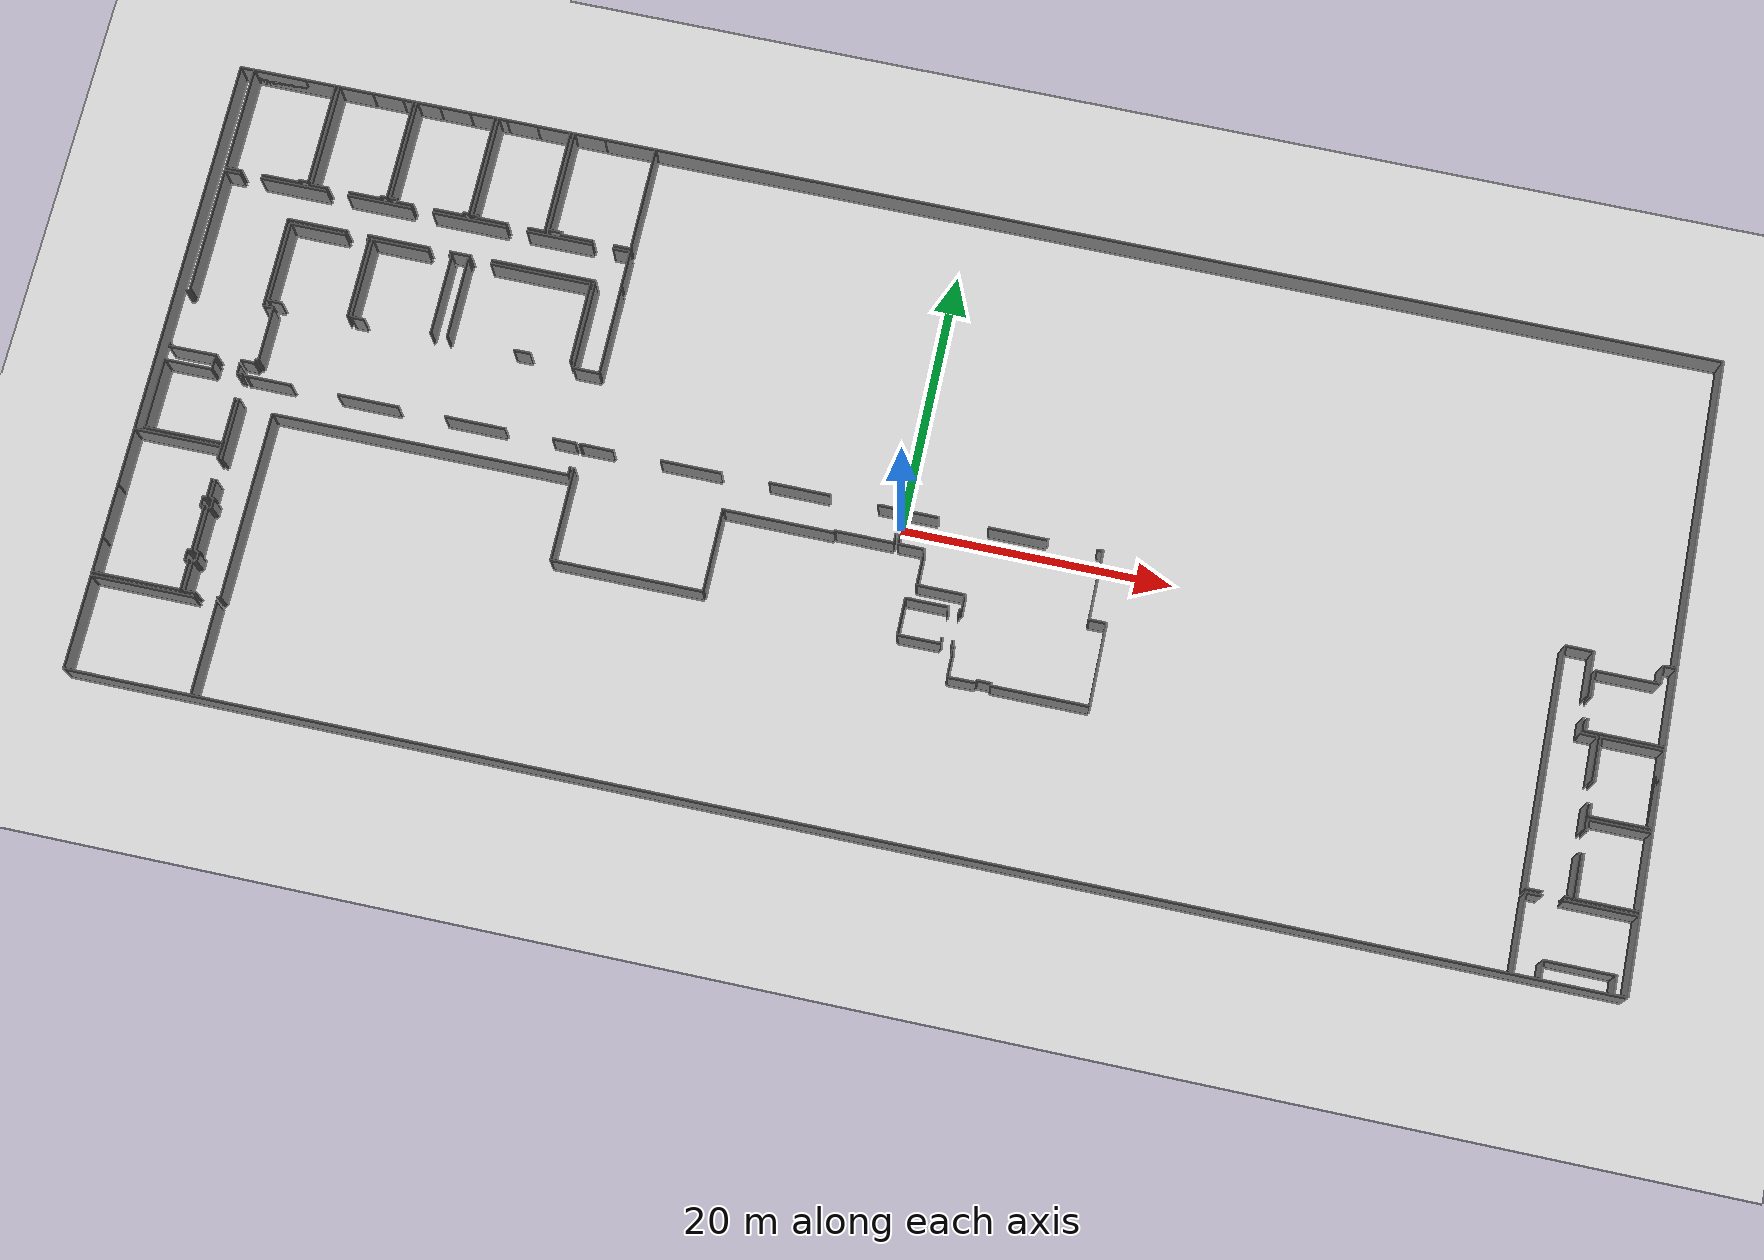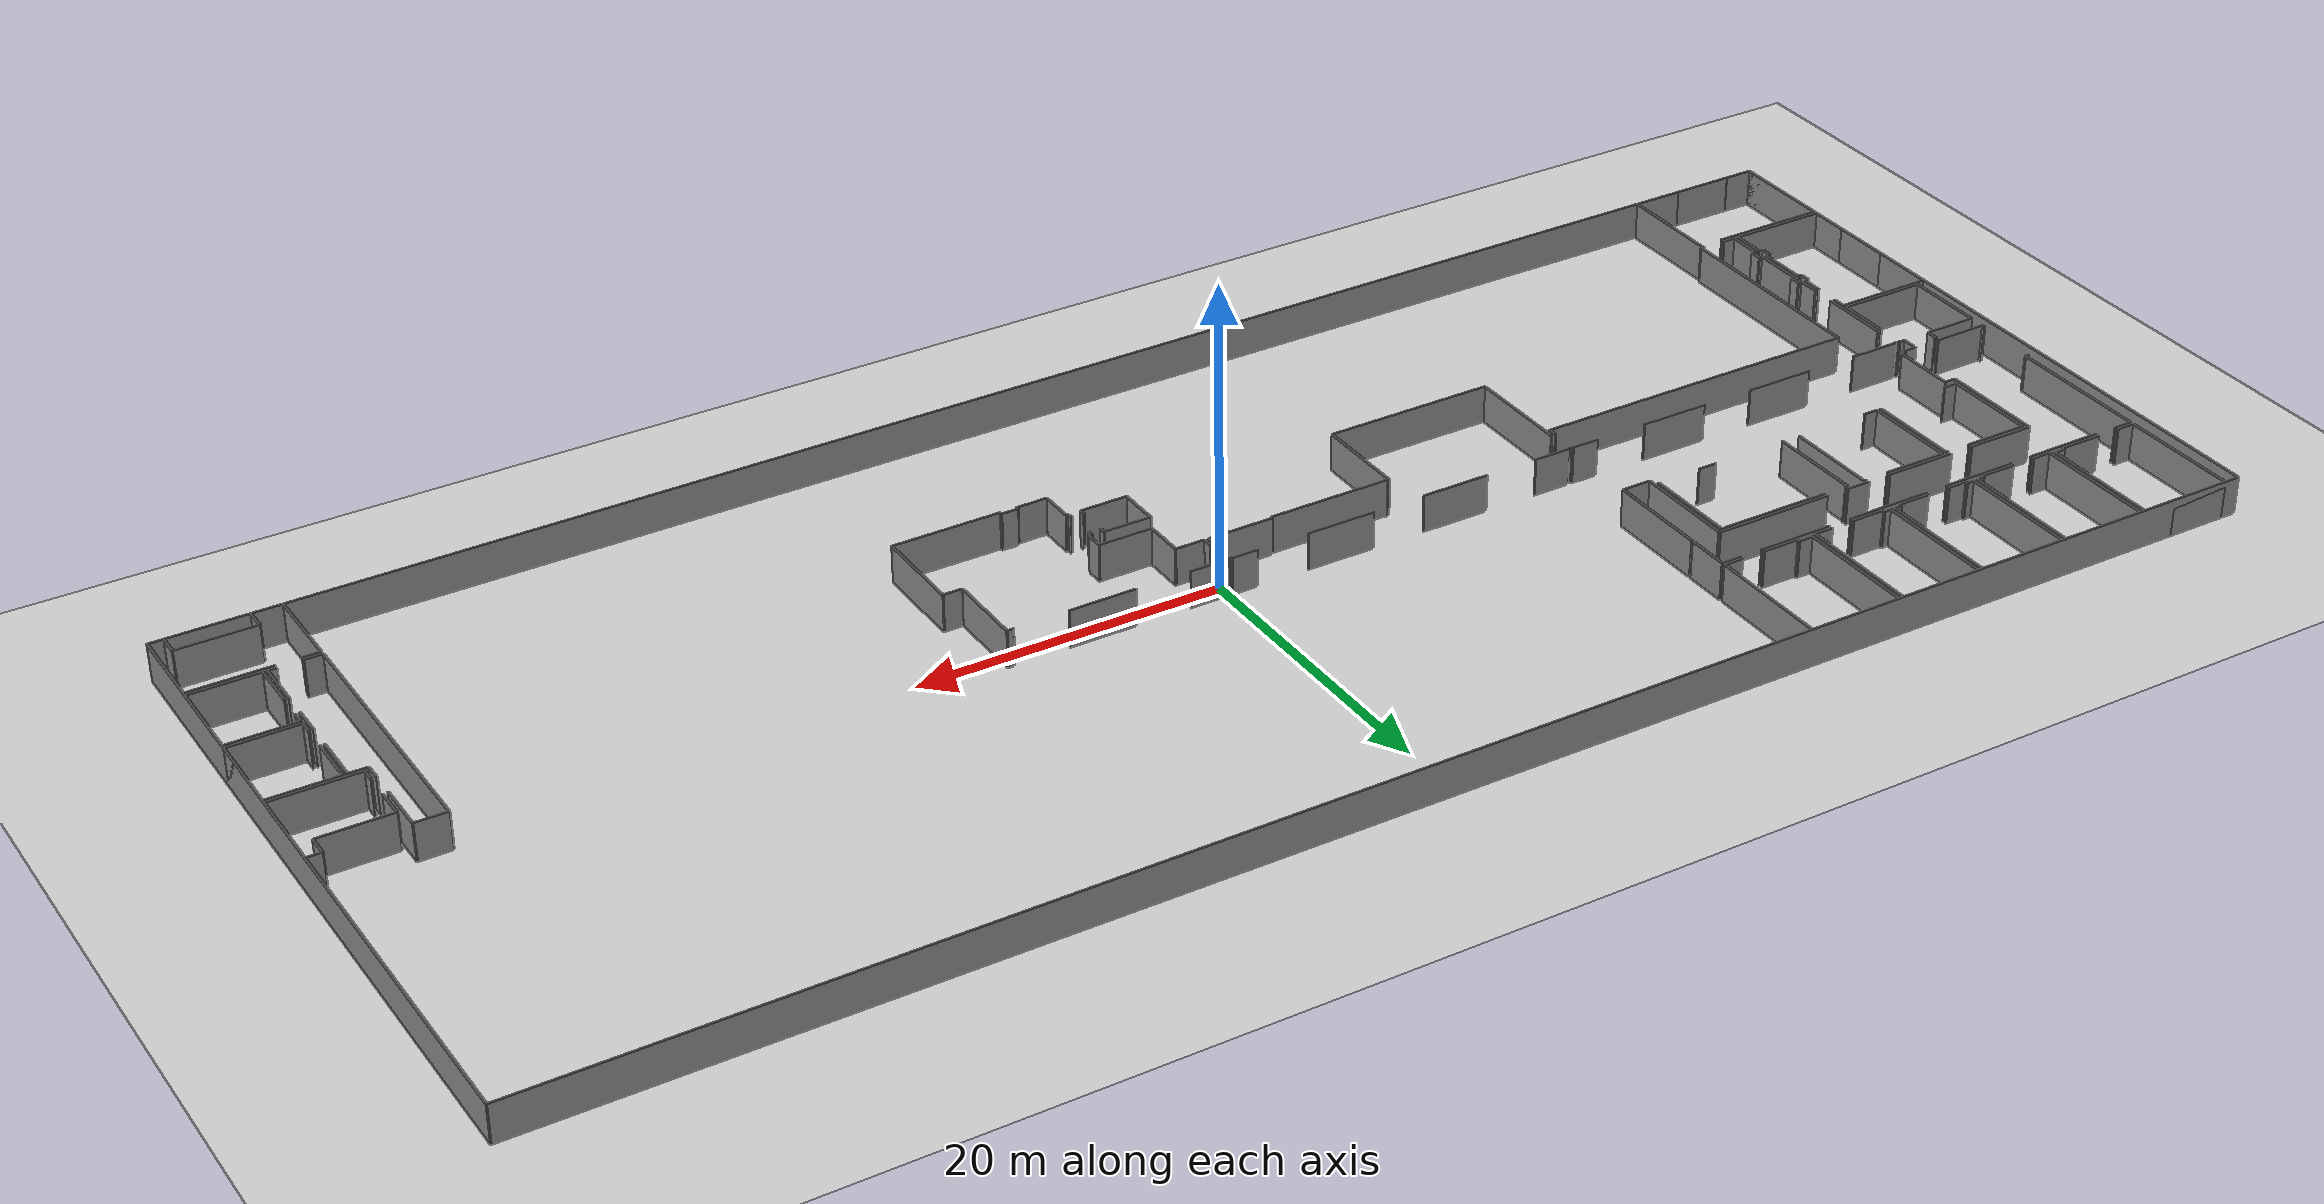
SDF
<sdf version="1.6">
  <world name="default">
    <light name="sun" type="directional">
      <cast_shadows>1</cast_shadows>
      <pose frame="">0 0 10 0 -0 0</pose>
      <diffuse>0.8 0.8 0.8 1</diffuse>
      <specular>0.1 0.1 0.1 1</specular>
      <attenuation>
        <range>1000</range>
        <constant>0.9</constant>
        <linear>0.01</linear>
        <quadratic>0.001</quadratic>
      </attenuation>
      <direction>-0.5 0.5 -1</direction>
    </light>
    <model name="ground_plane">
      <static>1</static>
      <link name="link">
        <collision name="collision">
          <geometry>
            <plane>
              <normal>0 0 1</normal>
              <size>100 100</size>
            </plane>
          </geometry>
          <surface>
            <friction>
              <ode>
                <mu>100</mu>
                <mu2>50</mu2>
              </ode>
              <torsional>
                <ode />
              </torsional>
            </friction>
            <contact>
              <ode />
            </contact>
            <bounce />
          </surface>
          <max_contacts>10</max_contacts>
        </collision>
        <visual name="visual">
          <cast_shadows>0</cast_shadows>
          <geometry>
            <plane>
              <normal>0 0 1</normal>
              <size>100 100</size>
            </plane>
          </geometry>
          <material>
            <script>
              <uri>file://media/materials/scripts/gazebo.material</uri>
              <name>Gazebo/Grey</name>
            </script>
          </material>
        </visual>
        <self_collide>0</self_collide>
        <kinematic>0</kinematic>
        <gravity>1</gravity>
      </link>
    </model>
    <gravity>0 0 -9.8</gravity>
    <magnetic_field>6e-06 2.3e-05 -4.2e-05</magnetic_field>
    <atmosphere type="adiabatic" />
    <physics default="0" name="default_physics" type="ode">
      <max_step_size>0.001</max_step_size>
      <real_time_factor>1</real_time_factor>
      <real_time_update_rate>1000</real_time_update_rate>
    </physics>
    <scene>
      <ambient>0.4 0.4 0.4 1</ambient>
      <background>0.7 0.7 0.7 1</background>
      <shadows>1</shadows>
    </scene>
    <spherical_coordinates>
      <surface_model>EARTH_WGS84</surface_model>
      <latitude_deg>0</latitude_deg>
      <longitude_deg>0</longitude_deg>
      <elevation>0</elevation>
      <heading_deg>0</heading_deg>
    </spherical_coordinates>
  <model name="50057024">
		<static>1</static>
		<link name="Wall_0">
			<collision name="Wall_0_Collision">
				<geometry>
					<box>
						<size>8.09425073079 0.1 2.5</size>
					</box>
				</geometry>
				<pose frame="">4.04712536539 0 1.25 0 0 0</pose>
			</collision>
			<visual name="Wall_0_Visual">
				<pose frame="">4.04712536539 0 1.25 0 0 0</pose>
				<geometry>
					<box>
						<size>8.09425073079 0.1 2.5</size>
					</box>
				</geometry>
				<material>
					<script>
						<uri>file://media/materials/scripts/gazebo.material</uri>
						<name>Gazebo/Grey</name>
					</script>
					<ambient>1 1 1 1</ambient>
				</material>
			</visual>
			<pose frame="">1.05245803928 -8.09425073079 0 0 0 1.57079632679</pose>
		</link>
		<link name="Wall_1">
			<collision name="Wall_1_Collision">
				<geometry>
					<box>
						<size>4.00058336028 0.1 2.5</size>
					</box>
				</geometry>
				<pose frame="">2.00029168014 0 1.25 0 0 0</pose>
			</collision>
			<visual name="Wall_1_Visual">
				<pose frame="">2.00029168014 0 1.25 0 0 0</pose>
				<geometry>
					<box>
						<size>4.00058336028 0.1 2.5</size>
					</box>
				</geometry>
				<material>
					<script>
						<uri>file://media/materials/scripts/gazebo.material</uri>
						<name>Gazebo/Grey</name>
					</script>
					<ambient>1 1 1 1</ambient>
				</material>
			</visual>
			<pose frame="">1.05245803928 -0.0 0 0 0 0.0</pose>
		</link>
		<link name="Wall_2">
			<collision name="Wall_2_Collision">
				<geometry>
					<box>
						<size>7.92000355089 0.1 2.5</size>
					</box>
				</geometry>
				<pose frame="">3.96000177544 0 1.25 0 0 0</pose>
			</collision>
			<visual name="Wall_2_Visual">
				<pose frame="">3.96000177544 0 1.25 0 0 0</pose>
				<geometry>
					<box>
						<size>7.92000355089 0.1 2.5</size>
					</box>
				</geometry>
				<material>
					<script>
						<uri>file://media/materials/scripts/gazebo.material</uri>
						<name>Gazebo/Grey</name>
					</script>
					<ambient>1 1 1 1</ambient>
				</material>
			</visual>
			<pose frame="">7.36606491785 -0.0 0 0 0 -1.57079632679</pose>
		</link>
		<link name="Wall_3">
			<collision name="Wall_3_Collision">
				<geometry>
					<box>
						<size>0.695340092704 0.1 2.5</size>
					</box>
				</geometry>
				<pose frame="">0.347670046352 0 1.25 0 0 0</pose>
			</collision>
			<visual name="Wall_3_Visual">
				<pose frame="">0.347670046352 0 1.25 0 0 0</pose>
				<geometry>
					<box>
						<size>0.695340092704 0.1 2.5</size>
					</box>
				</geometry>
				<material>
					<script>
						<uri>file://media/materials/scripts/gazebo.material</uri>
						<name>Gazebo/Grey</name>
					</script>
					<ambient>1 1 1 1</ambient>
				</material>
			</visual>
			<pose frame="">7.36606491785 -7.92000355089 0 0 0 3.14159265359</pose>
		</link>
		<link name="Wall_4">
			<collision name="Wall_4_Collision">
				<geometry>
					<box>
						<size>0.158521815772 0.1 2.5</size>
					</box>
				</geometry>
				<pose frame="">0.0792609078861 0 1.25 0 0 0</pose>
			</collision>
			<visual name="Wall_4_Visual">
				<pose frame="">0.0792609078861 0 1.25 0 0 0</pose>
				<geometry>
					<box>
						<size>0.158521815772 0.1 2.5</size>
					</box>
				</geometry>
				<material>
					<script>
						<uri>file://media/materials/scripts/gazebo.material</uri>
						<name>Gazebo/Grey</name>
					</script>
					<ambient>1 1 1 1</ambient>
				</material>
			</visual>
			<pose frame="">6.67072482515 -7.92000355089 0 0 0 -1.57079632679</pose>
		</link>
		<link name="Wall_5">
			<collision name="Wall_5_Collision">
				<geometry>
					<box>
						<size>2.81839106698 0.1 2.5</size>
					</box>
				</geometry>
				<pose frame="">1.40919553349 0 1.25 0 0 0</pose>
			</collision>
			<visual name="Wall_5_Visual">
				<pose frame="">1.40919553349 0 1.25 0 0 0</pose>
				<geometry>
					<box>
						<size>2.81839106698 0.1 2.5</size>
					</box>
				</geometry>
				<material>
					<script>
						<uri>file://media/materials/scripts/gazebo.material</uri>
						<name>Gazebo/Grey</name>
					</script>
					<ambient>1 1 1 1</ambient>
				</material>
			</visual>
			<pose frame="">6.67072482515 -8.07852536666 0 0 0 3.14159265359</pose>
		</link>
		<link name="Wall_6">
			<collision name="Wall_6_Collision">
				<geometry>
					<box>
						<size>1.22414306099 0.1 2.5</size>
					</box>
				</geometry>
				<pose frame="">0.612071530496 0 1.25 0 0 0</pose>
			</collision>
			<visual name="Wall_6_Visual">
				<pose frame="">0.612071530496 0 1.25 0 0 0</pose>
				<geometry>
					<box>
						<size>1.22414306099 0.1 2.5</size>
					</box>
				</geometry>
				<material>
					<script>
						<uri>file://media/materials/scripts/gazebo.material</uri>
						<name>Gazebo/Grey</name>
					</script>
					<ambient>1 1 1 1</ambient>
				</material>
			</visual>
			<pose frame="">2.27650009194 -8.07852536666 0 0 0 -3.12874628199</pose>
		</link>
		<link name="Wall_7">
			<collision name="Wall_7_Collision">
				<geometry>
					<box>
						<size>8.08372488222 0.1 2.5</size>
					</box>
				</geometry>
				<pose frame="">4.04186244111 0 1.25 0 0 0</pose>
			</collision>
			<visual name="Wall_7_Visual">
				<pose frame="">4.04186244111 0 1.25 0 0 0</pose>
				<geometry>
					<box>
						<size>8.08372488222 0.1 2.5</size>
					</box>
				</geometry>
				<material>
					<script>
						<uri>file://media/materials/scripts/gazebo.material</uri>
						<name>Gazebo/Grey</name>
					</script>
					<ambient>1 1 1 1</ambient>
				</material>
			</visual>
			<pose frame="">7.69008350929 -8.0947580006 0 0 0 1.57079632679</pose>
		</link>
		<link name="Wall_8">
			<collision name="Wall_8_Collision">
				<geometry>
					<box>
						<size>2.5699556773 0.1 2.5</size>
					</box>
				</geometry>
				<pose frame="">1.28497783865 0 1.25 0 0 0</pose>
			</collision>
			<visual name="Wall_8_Visual">
				<pose frame="">1.28497783865 0 1.25 0 0 0</pose>
				<geometry>
					<box>
						<size>2.5699556773 0.1 2.5</size>
					</box>
				</geometry>
				<material>
					<script>
						<uri>file://media/materials/scripts/gazebo.material</uri>
						<name>Gazebo/Grey</name>
					</script>
					<ambient>1 1 1 1</ambient>
				</material>
			</visual>
			<pose frame="">7.69008350929 -0.0110331183777 0 0 0 0.0</pose>
		</link>
		<link name="Wall_9">
			<collision name="Wall_9_Collision">
				<geometry>
					<box>
						<size>0.824693894374 0.1 2.5</size>
					</box>
				</geometry>
				<pose frame="">0.412346947187 0 1.25 0 0 0</pose>
			</collision>
			<visual name="Wall_9_Visual">
				<pose frame="">0.412346947187 0 1.25 0 0 0</pose>
				<geometry>
					<box>
						<size>0.824693894374 0.1 2.5</size>
					</box>
				</geometry>
				<material>
					<script>
						<uri>file://media/materials/scripts/gazebo.material</uri>
						<name>Gazebo/Grey</name>
					</script>
					<ambient>1 1 1 1</ambient>
				</material>
			</visual>
			<pose frame="">12.590183061 -0.0110331183777 0 0 0 0.0</pose>
		</link>
		<link name="Wall_10">
			<collision name="Wall_10_Collision">
				<geometry>
					<box>
						<size>7.89197689386 0.1 2.5</size>
					</box>
				</geometry>
				<pose frame="">3.94598844693 0 1.25 0 0 0</pose>
			</collision>
			<visual name="Wall_10_Visual">
				<pose frame="">3.94598844693 0 1.25 0 0 0</pose>
				<geometry>
					<box>
						<size>7.89197689386 0.1 2.5</size>
					</box>
				</geometry>
				<material>
					<script>
						<uri>file://media/materials/scripts/gazebo.material</uri>
						<name>Gazebo/Grey</name>
					</script>
					<ambient>1 1 1 1</ambient>
				</material>
			</visual>
			<pose frame="">13.4148769554 -0.0110331183777 0 0 0 -1.57079632679</pose>
		</link>
		<link name="Wall_11">
			<collision name="Wall_11_Collision">
				<geometry>
					<box>
						<size>0.460347353003 0.1 2.5</size>
					</box>
				</geometry>
				<pose frame="">0.230173676501 0 1.25 0 0 0</pose>
			</collision>
			<visual name="Wall_11_Visual">
				<pose frame="">0.230173676501 0 1.25 0 0 0</pose>
				<geometry>
					<box>
						<size>0.460347353003 0.1 2.5</size>
					</box>
				</geometry>
				<material>
					<script>
						<uri>file://media/materials/scripts/gazebo.material</uri>
						<name>Gazebo/Grey</name>
					</script>
					<ambient>1 1 1 1</ambient>
				</material>
			</visual>
			<pose frame="">13.4148769554 -7.90301001224 0 0 0 3.14159265359</pose>
		</link>
		<link name="Wall_12">
			<collision name="Wall_12_Collision">
				<geometry>
					<box>
						<size>0.172598553013 0.1 2.5</size>
					</box>
				</geometry>
				<pose frame="">0.0862992765064 0 1.25 0 0 0</pose>
			</collision>
			<visual name="Wall_12_Visual">
				<pose frame="">0.0862992765064 0 1.25 0 0 0</pose>
				<geometry>
					<box>
						<size>0.172598553013 0.1 2.5</size>
					</box>
				</geometry>
				<material>
					<script>
						<uri>file://media/materials/scripts/gazebo.material</uri>
						<name>Gazebo/Grey</name>
					</script>
					<ambient>1 1 1 1</ambient>
				</material>
			</visual>
			<pose frame="">12.9545296024 -7.90301001224 0 0 0 -1.57079632679</pose>
		</link>
		<link name="Wall_13">
			<collision name="Wall_13_Collision">
				<geometry>
					<box>
						<size>2.41993063085 0.1 2.5</size>
					</box>
				</geometry>
				<pose frame="">1.20996531543 0 1.25 0 0 0</pose>
			</collision>
			<visual name="Wall_13_Visual">
				<pose frame="">1.20996531543 0 1.25 0 0 0</pose>
				<geometry>
					<box>
						<size>2.41993063085 0.1 2.5</size>
					</box>
				</geometry>
				<material>
					<script>
						<uri>file://media/materials/scripts/gazebo.material</uri>
						<name>Gazebo/Grey</name>
					</script>
					<ambient>1 1 1 1</ambient>
				</material>
			</visual>
			<pose frame="">12.9545296024 -8.07560856525 0 0 0 3.14159265359</pose>
		</link>
		<link name="Wall_14">
			<collision name="Wall_14_Collision">
				<geometry>
					<box>
						<size>1.24955228471 0.1 2.5</size>
					</box>
				</geometry>
				<pose frame="">0.624776142356 0 1.25 0 0 0</pose>
			</collision>
			<visual name="Wall_14_Visual">
				<pose frame="">0.624776142356 0 1.25 0 0 0</pose>
				<geometry>
					<box>
						<size>1.24955228471 0.1 2.5</size>
					</box>
				</geometry>
				<material>
					<script>
						<uri>file://media/materials/scripts/gazebo.material</uri>
						<name>Gazebo/Grey</name>
					</script>
					<ambient>1 1 1 1</ambient>
				</material>
			</visual>
			<pose frame="">8.93948905248 -8.07560856525 0 0 0 -3.12626701638</pose>
		</link>
		<link name="Wall_15">
			<collision name="Wall_15_Collision">
				<geometry>
					<box>
						<size>7.90351728205 0.1 2.5</size>
					</box>
				</geometry>
				<pose frame="">3.95175864102 0 1.25 0 0 0</pose>
			</collision>
			<visual name="Wall_15_Visual">
				<pose frame="">3.95175864102 0 1.25 0 0 0</pose>
				<geometry>
					<box>
						<size>7.90351728205 0.1 2.5</size>
					</box>
				</geometry>
				<material>
					<script>
						<uri>file://media/materials/scripts/gazebo.material</uri>
						<name>Gazebo/Grey</name>
					</script>
					<ambient>1 1 1 1</ambient>
				</material>
			</visual>
			<pose frame="">13.7032598426 -7.91974991598 0 0 0 1.57079632679</pose>
		</link>
		<link name="Wall_16">
			<collision name="Wall_16_Collision">
				<geometry>
					<box>
						<size>1.74754449707 0.1 2.5</size>
					</box>
				</geometry>
				<pose frame="">0.873772248537 0 1.25 0 0 0</pose>
			</collision>
			<visual name="Wall_16_Visual">
				<pose frame="">0.873772248537 0 1.25 0 0 0</pose>
				<geometry>
					<box>
						<size>1.74754449707 0.1 2.5</size>
					</box>
				</geometry>
				<material>
					<script>
						<uri>file://media/materials/scripts/gazebo.material</uri>
						<name>Gazebo/Grey</name>
					</script>
					<ambient>1 1 1 1</ambient>
				</material>
			</visual>
			<pose frame="">13.7032598426 -0.0162326339351 0 0 0 0.0</pose>
		</link>
		<link name="Wall_17">
			<collision name="Wall_17_Collision">
				<geometry>
					<box>
						<size>1.92141122461 0.1 2.5</size>
					</box>
				</geometry>
				<pose frame="">0.960705612306 0 1.25 0 0 0</pose>
			</collision>
			<visual name="Wall_17_Visual">
				<pose frame="">0.960705612306 0 1.25 0 0 0</pose>
				<geometry>
					<box>
						<size>1.92141122461 0.1 2.5</size>
					</box>
				</geometry>
				<material>
					<script>
						<uri>file://media/materials/scripts/gazebo.material</uri>
						<name>Gazebo/Grey</name>
					</script>
					<ambient>1 1 1 1</ambient>
				</material>
			</visual>
			<pose frame="">17.7782850476 -0.0162326339351 0 0 0 0.0</pose>
		</link>
		<link name="Wall_18">
			<collision name="Wall_18_Collision">
				<geometry>
					<box>
						<size>7.8771392519 0.1 2.5</size>
					</box>
				</geometry>
				<pose frame="">3.93856962595 0 1.25 0 0 0</pose>
			</collision>
			<visual name="Wall_18_Visual">
				<pose frame="">3.93856962595 0 1.25 0 0 0</pose>
				<geometry>
					<box>
						<size>7.8771392519 0.1 2.5</size>
					</box>
				</geometry>
				<material>
					<script>
						<uri>file://media/materials/scripts/gazebo.material</uri>
						<name>Gazebo/Grey</name>
					</script>
					<ambient>1 1 1 1</ambient>
				</material>
			</visual>
			<pose frame="">19.6996962722 -0.0162326339351 0 0 0 -1.57079632679</pose>
		</link>
		<link name="Wall_19">
			<collision name="Wall_19_Collision">
				<geometry>
					<box>
						<size>0.435364314837 0.1 2.5</size>
					</box>
				</geometry>
				<pose frame="">0.217682157419 0 1.25 0 0 0</pose>
			</collision>
			<visual name="Wall_19_Visual">
				<pose frame="">0.217682157419 0 1.25 0 0 0</pose>
				<geometry>
					<box>
						<size>0.435364314837 0.1 2.5</size>
					</box>
				</geometry>
				<material>
					<script>
						<uri>file://media/materials/scripts/gazebo.material</uri>
						<name>Gazebo/Grey</name>
					</script>
					<ambient>1 1 1 1</ambient>
				</material>
			</visual>
			<pose frame="">19.6996962722 -7.89337188584 0 0 0 3.14159265359</pose>
		</link>
		<link name="Wall_20">
			<collision name="Wall_20_Collision">
				<geometry>
					<box>
						<size>0.182236679412 0.1 2.5</size>
					</box>
				</geometry>
				<pose frame="">0.0911183397059 0 1.25 0 0 0</pose>
			</collision>
			<visual name="Wall_20_Visual">
				<pose frame="">0.0911183397059 0 1.25 0 0 0</pose>
				<geometry>
					<box>
						<size>0.182236679412 0.1 2.5</size>
					</box>
				</geometry>
				<material>
					<script>
						<uri>file://media/materials/scripts/gazebo.material</uri>
						<name>Gazebo/Grey</name>
					</script>
					<ambient>1 1 1 1</ambient>
				</material>
			</visual>
			<pose frame="">19.2643319574 -7.89337188584 0 0 0 -1.57079632679</pose>
		</link>
		<link name="Wall_21">
			<collision name="Wall_21_Collision">
				<geometry>
					<box>
						<size>2.21841769864 0.1 2.5</size>
					</box>
				</geometry>
				<pose frame="">1.10920884932 0 1.25 0 0 0</pose>
			</collision>
			<visual name="Wall_21_Visual">
				<pose frame="">1.10920884932 0 1.25 0 0 0</pose>
				<geometry>
					<box>
						<size>2.21841769864 0.1 2.5</size>
					</box>
				</geometry>
				<material>
					<script>
						<uri>file://media/materials/scripts/gazebo.material</uri>
						<name>Gazebo/Grey</name>
					</script>
					<ambient>1 1 1 1</ambient>
				</material>
			</visual>
			<pose frame="">19.2643319574 -8.07560856525 0 0 0 3.14159265359</pose>
		</link>
		<link name="Wall_22">
			<collision name="Wall_22_Collision">
				<geometry>
					<box>
						<size>1.23913332953 0.1 2.5</size>
					</box>
				</geometry>
				<pose frame="">0.619566664764 0 1.25 0 0 0</pose>
			</collision>
			<visual name="Wall_22_Visual">
				<pose frame="">0.619566664764 0 1.25 0 0 0</pose>
				<geometry>
					<box>
						<size>1.23913332953 0.1 2.5</size>
					</box>
				</geometry>
				<material>
					<script>
						<uri>file://media/materials/scripts/gazebo.material</uri>
						<name>Gazebo/Grey</name>
					</script>
					<ambient>1 1 1 1</ambient>
				</material>
			</visual>
			<pose frame="">15.4689392354 -8.07560856525 0 0 0 3.14159265359</pose>
		</link>
		<link name="Wall_23">
			<collision name="Wall_23_Collision">
				<geometry>
					<box>
						<size>0.177924886023 0.1 2.5</size>
					</box>
				</geometry>
				<pose frame="">0.0889624430114 0 1.25 0 0 0</pose>
			</collision>
			<visual name="Wall_23_Visual">
				<pose frame="">0.0889624430114 0 1.25 0 0 0</pose>
				<geometry>
					<box>
						<size>0.177924886023 0.1 2.5</size>
					</box>
				</geometry>
				<material>
					<script>
						<uri>file://media/materials/scripts/gazebo.material</uri>
						<name>Gazebo/Grey</name>
					</script>
					<ambient>1 1 1 1</ambient>
				</material>
			</visual>
			<pose frame="">14.2298059059 -8.07560856525 0 0 0 1.57079632679</pose>
		</link>
		<link name="Wall_24">
			<collision name="Wall_24_Collision">
				<geometry>
					<box>
						<size>0.527008231007 0.1 2.5</size>
					</box>
				</geometry>
				<pose frame="">0.263504115503 0 1.25 0 0 0</pose>
			</collision>
			<visual name="Wall_24_Visual">
				<pose frame="">0.263504115503 0 1.25 0 0 0</pose>
				<geometry>
					<box>
						<size>0.527008231007 0.1 2.5</size>
					</box>
				</geometry>
				<material>
					<script>
						<uri>file://media/materials/scripts/gazebo.material</uri>
						<name>Gazebo/Grey</name>
					</script>
					<ambient>1 1 1 1</ambient>
				</material>
			</visual>
			<pose frame="">14.2298059059 -7.89768367923 0 0 0 -3.09970964653</pose>
		</link>
		<link name="Wall_25">
			<collision name="Wall_25_Collision">
				<geometry>
					<box>
						<size>7.91315540845 0.1 2.5</size>
					</box>
				</geometry>
				<pose frame="">3.95657770422 0 1.25 0 0 0</pose>
			</collision>
			<visual name="Wall_25_Visual">
				<pose frame="">3.95657770422 0 1.25 0 0 0</pose>
				<geometry>
					<box>
						<size>7.91315540845 0.1 2.5</size>
					</box>
				</geometry>
				<material>
					<script>
						<uri>file://media/materials/scripts/gazebo.material</uri>
						<name>Gazebo/Grey</name>
					</script>
					<ambient>1 1 1 1</ambient>
				</material>
			</visual>
			<pose frame="">20.003931341 -7.92837350276 0 0 0 1.57079632679</pose>
		</link>
		<link name="Wall_26">
			<collision name="Wall_26_Collision">
				<geometry>
					<box>
						<size>0.617093724438 0.1 2.5</size>
					</box>
				</geometry>
				<pose frame="">0.308546862219 0 1.25 0 0 0</pose>
			</collision>
			<visual name="Wall_26_Visual">
				<pose frame="">0.308546862219 0 1.25 0 0 0</pose>
				<geometry>
					<box>
						<size>0.617093724438 0.1 2.5</size>
					</box>
				</geometry>
				<material>
					<script>
						<uri>file://media/materials/scripts/gazebo.material</uri>
						<name>Gazebo/Grey</name>
					</script>
					<ambient>1 1 1 1</ambient>
				</material>
			</visual>
			<pose frame="">20.003931341 -0.0152180943141 0 0 0 0.0</pose>
		</link>
		<link name="Wall_27">
			<collision name="Wall_27_Collision">
				<geometry>
					<box>
						<size>2.54877716271 0.1 2.5</size>
					</box>
				</geometry>
				<pose frame="">1.27438858136 0 1.25 0 0 0</pose>
			</collision>
			<visual name="Wall_27_Visual">
				<pose frame="">1.27438858136 0 1.25 0 0 0</pose>
				<geometry>
					<box>
						<size>2.54877716271 0.1 2.5</size>
					</box>
				</geometry>
				<material>
					<script>
						<uri>file://media/materials/scripts/gazebo.material</uri>
						<name>Gazebo/Grey</name>
					</script>
					<ambient>1 1 1 1</ambient>
				</material>
			</visual>
			<pose frame="">22.9723474545 -0.0152180943141 0 0 0 0.0</pose>
		</link>
		<link name="Wall_28">
			<collision name="Wall_28_Collision">
				<geometry>
					<box>
						<size>8.04834281294 0.1 2.5</size>
					</box>
				</geometry>
				<pose frame="">4.02417140647 0 1.25 0 0 0</pose>
			</collision>
			<visual name="Wall_28_Visual">
				<pose frame="">4.02417140647 0 1.25 0 0 0</pose>
				<geometry>
					<box>
						<size>8.04834281294 0.1 2.5</size>
					</box>
				</geometry>
				<material>
					<script>
						<uri>file://media/materials/scripts/gazebo.material</uri>
						<name>Gazebo/Grey</name>
					</script>
					<ambient>1 1 1 1</ambient>
				</material>
			</visual>
			<pose frame="">25.5211246172 -0.0152180943141 0 0 0 -1.57079632679</pose>
		</link>
		<link name="Wall_29">
			<collision name="Wall_29_Collision">
				<geometry>
					<box>
						<size>1.25866321723 0.1 2.5</size>
					</box>
				</geometry>
				<pose frame="">0.629331608616 0 1.25 0 0 0</pose>
			</collision>
			<visual name="Wall_29_Visual">
				<pose frame="">0.629331608616 0 1.25 0 0 0</pose>
				<geometry>
					<box>
						<size>1.25866321723 0.1 2.5</size>
					</box>
				</geometry>
				<material>
					<script>
						<uri>file://media/materials/scripts/gazebo.material</uri>
						<name>Gazebo/Grey</name>
					</script>
					<ambient>1 1 1 1</ambient>
				</material>
			</visual>
			<pose frame="">25.5211246172 -8.06356090725 0 0 0 3.14159265359</pose>
		</link>
		<link name="Wall_30">
			<collision name="Wall_30_Collision">
				<geometry>
					<box>
						<size>2.2043409614 0.1 2.5</size>
					</box>
				</geometry>
				<pose frame="">1.1021704807 0 1.25 0 0 0</pose>
			</collision>
			<visual name="Wall_30_Visual">
				<pose frame="">1.1021704807 0 1.25 0 0 0</pose>
				<geometry>
					<box>
						<size>2.2043409614 0.1 2.5</size>
					</box>
				</geometry>
				<material>
					<script>
						<uri>file://media/materials/scripts/gazebo.material</uri>
						<name>Gazebo/Grey</name>
					</script>
					<ambient>1 1 1 1</ambient>
				</material>
			</visual>
			<pose frame="">22.6871350035 -8.06356090725 0 0 0 3.14159265359</pose>
		</link>
		<link name="Wall_31">
			<collision name="Wall_31_Collision">
				<geometry>
					<box>
						<size>0.15116640352 0.1 2.5</size>
					</box>
				</geometry>
				<pose frame="">0.0755832017602 0 1.25 0 0 0</pose>
			</collision>
			<visual name="Wall_31_Visual">
				<pose frame="">0.0755832017602 0 1.25 0 0 0</pose>
				<geometry>
					<box>
						<size>0.15116640352 0.1 2.5</size>
					</box>
				</geometry>
				<material>
					<script>
						<uri>file://media/materials/scripts/gazebo.material</uri>
						<name>Gazebo/Grey</name>
					</script>
					<ambient>1 1 1 1</ambient>
				</material>
			</visual>
			<pose frame="">20.4827940421 -8.06356090725 0 0 0 1.57079632679</pose>
		</link>
		<link name="Wall_32">
			<collision name="Wall_32_Collision">
				<geometry>
					<box>
						<size>0.47912922568 0.1 2.5</size>
					</box>
				</geometry>
				<pose frame="">0.23956461284 0 1.25 0 0 0</pose>
			</collision>
			<visual name="Wall_32_Visual">
				<pose frame="">0.23956461284 0 1.25 0 0 0</pose>
				<geometry>
					<box>
						<size>0.47912922568 0.1 2.5</size>
					</box>
				</geometry>
				<material>
					<script>
						<uri>file://media/materials/scripts/gazebo.material</uri>
						<name>Gazebo/Grey</name>
					</script>
					<ambient>1 1 1 1</ambient>
				</material>
			</visual>
			<pose frame="">20.4827940421 -7.91239450373 0 0 0 -3.10823638621</pose>
		</link>
		<link name="Wall_33">
			<collision name="Wall_33_Collision">
				<geometry>
					<box>
						<size>7.90554636129 0.1 2.5</size>
					</box>
				</geometry>
				<pose frame="">3.95277318065 0 1.25 0 0 0</pose>
			</collision>
			<visual name="Wall_33_Visual">
				<pose frame="">3.95277318065 0 1.25 0 0 0</pose>
				<geometry>
					<box>
						<size>7.90554636129 0.1 2.5</size>
					</box>
				</geometry>
				<material>
					<script>
						<uri>file://media/materials/scripts/gazebo.material</uri>
						<name>Gazebo/Grey</name>
					</script>
					<ambient>1 1 1 1</ambient>
				</material>
			</visual>
			<pose frame="">25.8339832728 -7.91239450373 0 0 0 1.57079632679</pose>
		</link>
		<link name="Wall_34">
			<collision name="Wall_34_Collision">
				<geometry>
					<box>
						<size>3.89405670008 0.1 2.5</size>
					</box>
				</geometry>
				<pose frame="">1.94702835004 0 1.25 0 0 0</pose>
			</collision>
			<visual name="Wall_34_Visual">
				<pose frame="">1.94702835004 0 1.25 0 0 0</pose>
				<geometry>
					<box>
						<size>3.89405670008 0.1 2.5</size>
					</box>
				</geometry>
				<material>
					<script>
						<uri>file://media/materials/scripts/gazebo.material</uri>
						<name>Gazebo/Grey</name>
					</script>
					<ambient>1 1 1 1</ambient>
				</material>
			</visual>
			<pose frame="">28.1755407179 -0.00684814244136 0 0 0 0.0</pose>
		</link>
		<link name="Wall_35">
			<collision name="Wall_35_Collision">
				<geometry>
					<box>
						<size>8.07827173176 0.1 2.5</size>
					</box>
				</geometry>
				<pose frame="">4.03913586588 0 1.25 0 0 0</pose>
			</collision>
			<visual name="Wall_35_Visual">
				<pose frame="">4.03913586588 0 1.25 0 0 0</pose>
				<geometry>
					<box>
						<size>8.07827173176 0.1 2.5</size>
					</box>
				</geometry>
				<material>
					<script>
						<uri>file://media/materials/scripts/gazebo.material</uri>
						<name>Gazebo/Grey</name>
					</script>
					<ambient>1 1 1 1</ambient>
				</material>
			</visual>
			<pose frame="">32.069597418 -0.00684814244136 0 0 0 -1.57079632679</pose>
		</link>
		<link name="Wall_36">
			<collision name="Wall_36_Collision">
				<geometry>
					<box>
						<size>1.25993139176 0.1 2.5</size>
					</box>
				</geometry>
				<pose frame="">0.629965695879 0 1.25 0 0 0</pose>
			</collision>
			<visual name="Wall_36_Visual">
				<pose frame="">0.629965695879 0 1.25 0 0 0</pose>
				<geometry>
					<box>
						<size>1.25993139176 0.1 2.5</size>
					</box>
				</geometry>
				<material>
					<script>
						<uri>file://media/materials/scripts/gazebo.material</uri>
						<name>Gazebo/Grey</name>
					</script>
					<ambient>1 1 1 1</ambient>
				</material>
			</visual>
			<pose frame="">32.069597418 -8.0851198742 0 0 0 3.14159265359</pose>
		</link>
		<link name="Wall_37">
			<collision name="Wall_37_Collision">
				<geometry>
					<box>
						<size>2.41840882142 0.1 2.5</size>
					</box>
				</geometry>
				<pose frame="">1.20920441071 0 1.25 0 0 0</pose>
			</collision>
			<visual name="Wall_37_Visual">
				<pose frame="">1.20920441071 0 1.25 0 0 0</pose>
				<geometry>
					<box>
						<size>2.41840882142 0.1 2.5</size>
					</box>
				</geometry>
				<material>
					<script>
						<uri>file://media/materials/scripts/gazebo.material</uri>
						<name>Gazebo/Grey</name>
					</script>
					<ambient>1 1 1 1</ambient>
				</material>
			</visual>
			<pose frame="">29.2274914874 -8.0851198742 0 0 0 3.14159265359</pose>
		</link>
		<link name="Wall_38">
			<collision name="Wall_38_Collision">
				<geometry>
					<box>
						<size>0.182743949222 0.1 2.5</size>
					</box>
				</geometry>
				<pose frame="">0.0913719746111 0 1.25 0 0 0</pose>
			</collision>
			<visual name="Wall_38_Visual">
				<pose frame="">0.0913719746111 0 1.25 0 0 0</pose>
				<geometry>
					<box>
						<size>0.182743949222 0.1 2.5</size>
					</box>
				</geometry>
				<material>
					<script>
						<uri>file://media/materials/scripts/gazebo.material</uri>
						<name>Gazebo/Grey</name>
					</script>
					<ambient>1 1 1 1</ambient>
				</material>
			</visual>
			<pose frame="">26.809082666 -8.0851198742 0 0 0 1.57079632679</pose>
		</link>
		<link name="Wall_39">
			<collision name="Wall_39_Collision">
				<geometry>
					<box>
						<size>0.975150859353 0.1 2.5</size>
					</box>
				</geometry>
				<pose frame="">0.487575429677 0 1.25 0 0 0</pose>
			</collision>
			<visual name="Wall_39_Visual">
				<pose frame="">0.487575429677 0 1.25 0 0 0</pose>
				<geometry>
					<box>
						<size>0.975150859353 0.1 2.5</size>
					</box>
				</geometry>
				<material>
					<script>
						<uri>file://media/materials/scripts/gazebo.material</uri>
						<name>Gazebo/Grey</name>
					</script>
					<ambient>1 1 1 1</ambient>
				</material>
			</visual>
			<pose frame="">26.809082666 -7.90237592497 0 0 0 -3.1313185971</pose>
		</link>
		<link name="Wall_40">
			<collision name="Wall_40_Collision">
				<geometry>
					<box>
						<size>9.60439295656 0.1 2.5</size>
					</box>
				</geometry>
				<pose frame="">4.80219647828 0 1.25 0 0 0</pose>
			</collision>
			<visual name="Wall_40_Visual">
				<pose frame="">4.80219647828 0 1.25 0 0 0</pose>
				<geometry>
					<box>
						<size>9.60439295656 0.1 2.5</size>
					</box>
				</geometry>
				<material>
					<script>
						<uri>file://media/materials/scripts/gazebo.material</uri>
						<name>Gazebo/Grey</name>
					</script>
					<ambient>1 1 1 1</ambient>
				</material>
			</visual>
			<pose frame="">1.04307354778 -17.9446695454 0 0 0 1.57079632679</pose>
		</link>
		<link name="Wall_41">
			<collision name="Wall_41_Collision">
				<geometry>
					<box>
						<size>1.2400210517 0.1 2.5</size>
					</box>
				</geometry>
				<pose frame="">0.620010525849 0 1.25 0 0 0</pose>
			</collision>
			<visual name="Wall_41_Visual">
				<pose frame="">0.620010525849 0 1.25 0 0 0</pose>
				<geometry>
					<box>
						<size>1.2400210517 0.1 2.5</size>
					</box>
				</geometry>
				<material>
					<script>
						<uri>file://media/materials/scripts/gazebo.material</uri>
						<name>Gazebo/Grey</name>
					</script>
					<ambient>1 1 1 1</ambient>
				</material>
			</visual>
			<pose frame="">1.04307354778 -8.34027658886 0 0 0 0.0</pose>
		</link>
		<link name="Wall_42">
			<collision name="Wall_42_Collision">
				<geometry>
					<box>
						<size>5.09451070656 0.1 2.5</size>
					</box>
				</geometry>
				<pose frame="">2.54725535328 0 1.25 0 0 0</pose>
			</collision>
			<visual name="Wall_42_Visual">
				<pose frame="">2.54725535328 0 1.25 0 0 0</pose>
				<geometry>
					<box>
						<size>5.09451070656 0.1 2.5</size>
					</box>
				</geometry>
				<material>
					<script>
						<uri>file://media/materials/scripts/gazebo.material</uri>
						<name>Gazebo/Grey</name>
					</script>
					<ambient>1 1 1 1</ambient>
				</material>
			</visual>
			<pose frame="">3.83965201291 -8.34027658886 0 0 0 0.0</pose>
		</link>
		<link name="Wall_43">
			<collision name="Wall_43_Collision">
				<geometry>
					<box>
						<size>4.94867063605 0.1 2.5</size>
					</box>
				</geometry>
				<pose frame="">2.47433531803 0 1.25 0 0 0</pose>
			</collision>
			<visual name="Wall_43_Visual">
				<pose frame="">2.47433531803 0 1.25 0 0 0</pose>
				<geometry>
					<box>
						<size>4.94867063605 0.1 2.5</size>
					</box>
				</geometry>
				<material>
					<script>
						<uri>file://media/materials/scripts/gazebo.material</uri>
						<name>Gazebo/Grey</name>
					</script>
					<ambient>1 1 1 1</ambient>
				</material>
			</visual>
			<pose frame="">10.5093622984 -8.34027658886 0 0 0 0.0</pose>
		</link>
		<link name="Wall_44">
			<collision name="Wall_44_Collision">
				<geometry>
					<box>
						<size>5.66176517212 0.1 2.5</size>
					</box>
				</geometry>
				<pose frame="">2.83088258606 0 1.25 0 0 0</pose>
			</collision>
			<visual name="Wall_44_Visual">
				<pose frame="">2.83088258606 0 1.25 0 0 0</pose>
				<geometry>
					<box>
						<size>5.66176517212 0.1 2.5</size>
					</box>
				</geometry>
				<material>
					<script>
						<uri>file://media/materials/scripts/gazebo.material</uri>
						<name>Gazebo/Grey</name>
					</script>
					<ambient>1 1 1 1</ambient>
				</material>
			</visual>
			<pose frame="">17.0205507682 -8.34027658886 0 0 0 0.0</pose>
		</link>
		<link name="Wall_45">
			<collision name="Wall_45_Collision">
				<geometry>
					<box>
						<size>4.98646223693 0.1 2.5</size>
					</box>
				</geometry>
				<pose frame="">2.49323111847 0 1.25 0 0 0</pose>
			</collision>
			<visual name="Wall_45_Visual">
				<pose frame="">2.49323111847 0 1.25 0 0 0</pose>
				<geometry>
					<box>
						<size>4.98646223693 0.1 2.5</size>
					</box>
				</geometry>
				<material>
					<script>
						<uri>file://media/materials/scripts/gazebo.material</uri>
						<name>Gazebo/Grey</name>
					</script>
					<ambient>1 1 1 1</ambient>
				</material>
			</visual>
			<pose frame="">24.2506673768 -8.34027658886 0 0 0 0.0</pose>
		</link>
		<link name="Wall_46">
			<collision name="Wall_46_Collision">
				<geometry>
					<box>
						<size>1.29252347708 0.1 2.5</size>
					</box>
				</geometry>
				<pose frame="">0.64626173854 0 1.25 0 0 0</pose>
			</collision>
			<visual name="Wall_46_Visual">
				<pose frame="">0.64626173854 0 1.25 0 0 0</pose>
				<geometry>
					<box>
						<size>1.29252347708 0.1 2.5</size>
					</box>
				</geometry>
				<material>
					<script>
						<uri>file://media/materials/scripts/gazebo.material</uri>
						<name>Gazebo/Grey</name>
					</script>
					<ambient>1 1 1 1</ambient>
				</material>
			</visual>
			<pose frame="">30.7938138447 -8.34027658886 0 0 0 0.0</pose>
		</link>
		<link name="Wall_47">
			<collision name="Wall_47_Collision">
				<geometry>
					<box>
						<size>2.76474728452 0.1 2.5</size>
					</box>
				</geometry>
				<pose frame="">1.38237364226 0 1.25 0 0 0</pose>
			</collision>
			<visual name="Wall_47_Visual">
				<pose frame="">1.38237364226 0 1.25 0 0 0</pose>
				<geometry>
					<box>
						<size>2.76474728452 0.1 2.5</size>
					</box>
				</geometry>
				<material>
					<script>
						<uri>file://media/materials/scripts/gazebo.material</uri>
						<name>Gazebo/Grey</name>
					</script>
					<ambient>1 1 1 1</ambient>
				</material>
			</visual>
			<pose frame="">32.0863373217 -8.34027658886 0 0 0 -1.57079632679</pose>
		</link>
		<link name="Wall_48">
			<collision name="Wall_48_Collision">
				<geometry>
					<box>
						<size>7.89032826698 0.1 2.5</size>
					</box>
				</geometry>
				<pose frame="">3.94516413349 0 1.25 0 0 0</pose>
			</collision>
			<visual name="Wall_48_Visual">
				<pose frame="">3.94516413349 0 1.25 0 0 0</pose>
				<geometry>
					<box>
						<size>7.89032826698 0.1 2.5</size>
					</box>
				</geometry>
				<material>
					<script>
						<uri>file://media/materials/scripts/gazebo.material</uri>
						<name>Gazebo/Grey</name>
					</script>
					<ambient>1 1 1 1</ambient>
				</material>
			</visual>
			<pose frame="">30.126500409 -11.1050238734 0 0 0 3.14159265359</pose>
		</link>
		<link name="Wall_49">
			<collision name="Wall_49_Collision">
				<geometry>
					<box>
						<size>1.60436759307 0.1 2.5</size>
					</box>
				</geometry>
				<pose frame="">0.802183796534 0 1.25 0 0 0</pose>
			</collision>
			<visual name="Wall_49_Visual">
				<pose frame="">0.802183796534 0 1.25 0 0 0</pose>
				<geometry>
					<box>
						<size>1.60436759307 0.1 2.5</size>
					</box>
				</geometry>
				<material>
					<script>
						<uri>file://media/materials/scripts/gazebo.material</uri>
						<name>Gazebo/Grey</name>
					</script>
					<ambient>1 1 1 1</ambient>
				</material>
			</visual>
			<pose frame="">20.6674402531 -11.1050238734 0 0 0 3.14159265359</pose>
		</link>
		<link name="Wall_50">
			<collision name="Wall_50_Collision">
				<geometry>
					<box>
						<size>4.72204784822 0.1 2.5</size>
					</box>
				</geometry>
				<pose frame="">2.36102392411 0 1.25 0 0 0</pose>
			</collision>
			<visual name="Wall_50_Visual">
				<pose frame="">2.36102392411 0 1.25 0 0 0</pose>
				<geometry>
					<box>
						<size>4.72204784822 0.1 2.5</size>
					</box>
				</geometry>
				<material>
					<script>
						<uri>file://media/materials/scripts/gazebo.material</uri>
						<name>Gazebo/Grey</name>
					</script>
					<ambient>1 1 1 1</ambient>
				</material>
			</visual>
			<pose frame="">17.4964966679 -11.1050238734 0 0 0 3.14159265359</pose>
		</link>
		<link name="Wall_51">
			<collision name="Wall_51_Collision">
				<geometry>
					<box>
						<size>4.5318216693 0.1 2.5</size>
					</box>
				</geometry>
				<pose frame="">2.26591083465 0 1.25 0 0 0</pose>
			</collision>
			<visual name="Wall_51_Visual">
				<pose frame="">2.26591083465 0 1.25 0 0 0</pose>
				<geometry>
					<box>
						<size>4.5318216693 0.1 2.5</size>
					</box>
				</geometry>
				<material>
					<script>
						<uri>file://media/materials/scripts/gazebo.material</uri>
						<name>Gazebo/Grey</name>
					</script>
					<ambient>1 1 1 1</ambient>
				</material>
			</visual>
			<pose frame="">11.2090141845 -11.1050238734 0 0 0 3.14159265359</pose>
		</link>
		<link name="Wall_52">
			<collision name="Wall_52_Collision">
				<geometry>
					<box>
						<size>6.91877976247 0.1 2.5</size>
					</box>
				</geometry>
				<pose frame="">3.45938988124 0 1.25 0 0 0</pose>
			</collision>
			<visual name="Wall_52_Visual">
				<pose frame="">3.45938988124 0 1.25 0 0 0</pose>
				<geometry>
					<box>
						<size>6.91877976247 0.1 2.5</size>
					</box>
				</geometry>
				<material>
					<script>
						<uri>file://media/materials/scripts/gazebo.material</uri>
						<name>Gazebo/Grey</name>
					</script>
					<ambient>1 1 1 1</ambient>
				</material>
			</visual>
			<pose frame="">6.67719251523 -11.1050238734 0 0 0 -1.57079632679</pose>
		</link>
		<link name="Wall_53">
			<collision name="Wall_53_Collision">
				<geometry>
					<box>
						<size>0.0800269373903 0.1 2.5</size>
					</box>
				</geometry>
				<pose frame="">0.0400134686951 0 1.25 0 0 0</pose>
			</collision>
			<visual name="Wall_53_Visual">
				<pose frame="">0.0400134686951 0 1.25 0 0 0</pose>
				<geometry>
					<box>
						<size>0.0800269373903 0.1 2.5</size>
					</box>
				</geometry>
				<material>
					<script>
						<uri>file://media/materials/scripts/gazebo.material</uri>
						<name>Gazebo/Grey</name>
					</script>
					<ambient>1 1 1 1</ambient>
				</material>
			</visual>
			<pose frame="">1.05499438833 -18.0238036359 0 0 0 1.72031313532</pose>
		</link>
		<link name="Wall_54">
			<collision name="Wall_54_Collision">
				<geometry>
					<box>
						<size>6.21240655139 0.1 2.5</size>
					</box>
				</geometry>
				<pose frame="">3.10620327569 0 1.25 0 0 0</pose>
			</collision>
			<visual name="Wall_54_Visual">
				<pose frame="">3.10620327569 0 1.25 0 0 0</pose>
				<geometry>
					<box>
						<size>6.21240655139 0.1 2.5</size>
					</box>
				</geometry>
				<material>
					<script>
						<uri>file://media/materials/scripts/gazebo.material</uri>
						<name>Gazebo/Grey</name>
					</script>
					<ambient>1 1 1 1</ambient>
				</material>
			</visual>
			<pose frame="">6.96544858503 -17.6149441686 0 0 0 1.57079632679</pose>
		</link>
		<link name="Wall_55">
			<collision name="Wall_55_Collision">
				<geometry>
					<box>
						<size>4.20552036371 0.1 2.5</size>
					</box>
				</geometry>
				<pose frame="">2.10276018186 0 1.25 0 0 0</pose>
			</collision>
			<visual name="Wall_55_Visual">
				<pose frame="">2.10276018186 0 1.25 0 0 0</pose>
				<geometry>
					<box>
						<size>4.20552036371 0.1 2.5</size>
					</box>
				</geometry>
				<material>
					<script>
						<uri>file://media/materials/scripts/gazebo.material</uri>
						<name>Gazebo/Grey</name>
					</script>
					<ambient>1 1 1 1</ambient>
				</material>
			</visual>
			<pose frame="">6.96544858503 -11.4025376172 0 0 0 0.0</pose>
		</link>
		<link name="Wall_56">
			<collision name="Wall_56_Collision">
				<geometry>
					<box>
						<size>0.175134902065 0.1 2.5</size>
					</box>
				</geometry>
				<pose frame="">0.0875674510326 0 1.25 0 0 0</pose>
			</collision>
			<visual name="Wall_56_Visual">
				<pose frame="">0.0875674510326 0 1.25 0 0 0</pose>
				<geometry>
					<box>
						<size>0.175134902065 0.1 2.5</size>
					</box>
				</geometry>
				<material>
					<script>
						<uri>file://media/materials/scripts/gazebo.material</uri>
						<name>Gazebo/Grey</name>
					</script>
					<ambient>1 1 1 1</ambient>
				</material>
			</visual>
			<pose frame="">12.7660788678 -11.4025376172 0 0 0 0.0</pose>
		</link>
		<link name="Wall_57">
			<collision name="Wall_57_Collision">
				<geometry>
					<box>
						<size>6.19401802076 0.1 2.5</size>
					</box>
				</geometry>
				<pose frame="">3.09700901038 0 1.25 0 0 0</pose>
			</collision>
			<visual name="Wall_57_Visual">
				<pose frame="">3.09700901038 0 1.25 0 0 0</pose>
				<geometry>
					<box>
						<size>6.19401802076 0.1 2.5</size>
					</box>
				</geometry>
				<material>
					<script>
						<uri>file://media/materials/scripts/gazebo.material</uri>
						<name>Gazebo/Grey</name>
					</script>
					<ambient>1 1 1 1</ambient>
				</material>
			</visual>
			<pose frame="">12.9412137698 -11.4025376172 0 0 0 -1.57079632679</pose>
		</link>
		<link name="Wall_58">
			<collision name="Wall_58_Collision">
				<geometry>
					<box>
						<size>0.965002396055 0.1 2.5</size>
					</box>
				</geometry>
				<pose frame="">0.482501198028 0 1.25 0 0 0</pose>
			</collision>
			<visual name="Wall_58_Visual">
				<pose frame="">0.482501198028 0 1.25 0 0 0</pose>
				<geometry>
					<box>
						<size>0.965002396055 0.1 2.5</size>
					</box>
				</geometry>
				<material>
					<script>
						<uri>file://media/materials/scripts/gazebo.material</uri>
						<name>Gazebo/Grey</name>
					</script>
					<ambient>1 1 1 1</ambient>
				</material>
			</visual>
			<pose frame="">7.93027576455 -17.596555638 0 0 0 -3.12253607536</pose>
		</link>
		<link name="Wall_59">
			<collision name="Wall_59_Collision">
				<geometry>
					<box>
						<size>6.21139201177 0.1 2.5</size>
					</box>
				</geometry>
				<pose frame="">3.10569600588 0 1.25 0 0 0</pose>
			</collision>
			<visual name="Wall_59_Visual">
				<pose frame="">3.10569600588 0 1.25 0 0 0</pose>
				<geometry>
					<box>
						<size>6.21139201177 0.1 2.5</size>
					</box>
				</geometry>
				<material>
					<script>
						<uri>file://media/materials/scripts/gazebo.material</uri>
						<name>Gazebo/Grey</name>
					</script>
					<ambient>1 1 1 1</ambient>
				</material>
			</visual>
			<pose frame="">13.240502958 -17.5869175116 0 0 0 1.57079632679</pose>
		</link>
		<link name="Wall_60">
			<collision name="Wall_60_Collision">
				<geometry>
					<box>
						<size>4.24521422638 0.1 2.5</size>
					</box>
				</geometry>
				<pose frame="">2.12260711319 0 1.25 0 0 0</pose>
			</collision>
			<visual name="Wall_60_Visual">
				<pose frame="">2.12260711319 0 1.25 0 0 0</pose>
				<geometry>
					<box>
						<size>4.24521422638 0.1 2.5</size>
					</box>
				</geometry>
				<material>
					<script>
						<uri>file://media/materials/scripts/gazebo.material</uri>
						<name>Gazebo/Grey</name>
					</script>
					<ambient>1 1 1 1</ambient>
				</material>
			</visual>
			<pose frame="">13.240502958 -11.3755254998 0 0 0 0.0</pose>
		</link>
		<link name="Wall_61">
			<collision name="Wall_61_Collision">
				<geometry>
					<box>
						<size>0.201766567115 0.1 2.5</size>
					</box>
				</geometry>
				<pose frame="">0.100883283557 0 1.25 0 0 0</pose>
			</collision>
			<visual name="Wall_61_Visual">
				<pose frame="">0.100883283557 0 1.25 0 0 0</pose>
				<geometry>
					<box>
						<size>0.201766567115 0.1 2.5</size>
					</box>
				</geometry>
				<material>
					<script>
						<uri>file://media/materials/scripts/gazebo.material</uri>
						<name>Gazebo/Grey</name>
					</script>
					<ambient>1 1 1 1</ambient>
				</material>
			</visual>
			<pose frame="">19.053814986 -11.3755254998 0 0 0 0.0</pose>
		</link>
		<link name="Wall_62">
			<collision name="Wall_62_Collision">
				<geometry>
					<box>
						<size>6.20505113914 0.1 2.5</size>
					</box>
				</geometry>
				<pose frame="">3.10252556957 0 1.25 0 0 0</pose>
			</collision>
			<visual name="Wall_62_Visual">
				<pose frame="">3.10252556957 0 1.25 0 0 0</pose>
				<geometry>
					<box>
						<size>6.20505113914 0.1 2.5</size>
					</box>
				</geometry>
				<material>
					<script>
						<uri>file://media/materials/scripts/gazebo.material</uri>
						<name>Gazebo/Grey</name>
					</script>
					<ambient>1 1 1 1</ambient>
				</material>
			</visual>
			<pose frame="">19.2555815531 -11.3755254998 0 0 0 -1.57079632679</pose>
		</link>
		<link name="Wall_63">
			<collision name="Wall_63_Collision">
				<geometry>
					<box>
						<size>0.971061937336 0.1 2.5</size>
					</box>
				</geometry>
				<pose frame="">0.485530968668 0 1.25 0 0 0</pose>
			</collision>
			<visual name="Wall_63_Visual">
				<pose frame="">0.485530968668 0 1.25 0 0 0</pose>
				<geometry>
					<box>
						<size>0.971061937336 0.1 2.5</size>
					</box>
				</geometry>
				<material>
					<script>
						<uri>file://media/materials/scripts/gazebo.material</uri>
						<name>Gazebo/Grey</name>
					</script>
					<ambient>1 1 1 1</ambient>
				</material>
			</visual>
			<pose frame="">14.2115441927 -17.580576639 0 0 0 -3.13506277383</pose>
		</link>
		<link name="Wall_64">
			<collision name="Wall_64_Collision">
				<geometry>
					<box>
						<size>6.20403659952 0.1 2.5</size>
					</box>
				</geometry>
				<pose frame="">3.10201829976 0 1.25 0 0 0</pose>
			</collision>
			<visual name="Wall_64_Visual">
				<pose frame="">3.10201829976 0 1.25 0 0 0</pose>
				<geometry>
					<box>
						<size>6.20403659952 0.1 2.5</size>
					</box>
				</geometry>
				<material>
					<script>
						<uri>file://media/materials/scripts/gazebo.material</uri>
						<name>Gazebo/Grey</name>
					</script>
					<ambient>1 1 1 1</ambient>
				</material>
			</visual>
			<pose frame="">20.4973780492 -17.5922438446 0 0 0 1.57079632679</pose>
		</link>
		<link name="Wall_65">
			<collision name="Wall_65_Collision">
				<geometry>
					<box>
						<size>0.137723753543 0.1 2.5</size>
					</box>
				</geometry>
				<pose frame="">0.0688618767715 0 1.25 0 0 0</pose>
			</collision>
			<visual name="Wall_65_Visual">
				<pose frame="">0.0688618767715 0 1.25 0 0 0</pose>
				<geometry>
					<box>
						<size>0.137723753543 0.1 2.5</size>
					</box>
				</geometry>
				<material>
					<script>
						<uri>file://media/materials/scripts/gazebo.material</uri>
						<name>Gazebo/Grey</name>
					</script>
					<ambient>1 1 1 1</ambient>
				</material>
			</visual>
			<pose frame="">20.4973780492 -11.3882072451 0 0 0 0.0</pose>
		</link>
		<link name="Wall_66">
			<collision name="Wall_66_Collision">
				<geometry>
					<box>
						<size>7.57391872269 0.1 2.5</size>
					</box>
				</geometry>
				<pose frame="">3.78695936135 0 1.25 0 0 0</pose>
			</collision>
			<visual name="Wall_66_Visual">
				<pose frame="">3.78695936135 0 1.25 0 0 0</pose>
				<geometry>
					<box>
						<size>7.57391872269 0.1 2.5</size>
					</box>
				</geometry>
				<material>
					<script>
						<uri>file://media/materials/scripts/gazebo.material</uri>
						<name>Gazebo/Grey</name>
					</script>
					<ambient>1 1 1 1</ambient>
				</material>
			</visual>
			<pose frame="">22.2385816736 -11.3882072451 0 0 0 0.0</pose>
		</link>
		<link name="Wall_67">
			<collision name="Wall_67_Collision">
				<geometry>
					<box>
						<size>6.2008661632 0.1 2.5</size>
					</box>
				</geometry>
				<pose frame="">3.1004330816 0 1.25 0 0 0</pose>
			</collision>
			<visual name="Wall_67_Visual">
				<pose frame="">3.1004330816 0 1.25 0 0 0</pose>
				<geometry>
					<box>
						<size>6.2008661632 0.1 2.5</size>
					</box>
				</geometry>
				<material>
					<script>
						<uri>file://media/materials/scripts/gazebo.material</uri>
						<name>Gazebo/Grey</name>
					</script>
					<ambient>1 1 1 1</ambient>
				</material>
			</visual>
			<pose frame="">29.8125003963 -11.3882072451 0 0 0 -1.57079632679</pose>
		</link>
		<link name="Wall_68">
			<collision name="Wall_68_Collision">
				<geometry>
					<box>
						<size>1.23989423424 0.1 2.5</size>
					</box>
				</geometry>
				<pose frame="">0.619947117122 0 1.25 0 0 0</pose>
			</collision>
			<visual name="Wall_68_Visual">
				<pose frame="">0.619947117122 0 1.25 0 0 0</pose>
				<geometry>
					<box>
						<size>1.23989423424 0.1 2.5</size>
					</box>
				</geometry>
				<material>
					<script>
						<uri>file://media/materials/scripts/gazebo.material</uri>
						<name>Gazebo/Grey</name>
					</script>
					<ambient>1 1 1 1</ambient>
				</material>
			</visual>
			<pose frame="">26.7983031825 -17.5890734083 0 0 0 3.14159265359</pose>
		</link>
		<link name="Wall_69">
			<collision name="Wall_69_Collision">
				<geometry>
					<box>
						<size>0.0219163160995 0.1 2.5</size>
					</box>
				</geometry>
				<pose frame="">0.0109581580497 0 1.25 0 0 0</pose>
			</collision>
			<visual name="Wall_69_Visual">
				<pose frame="">0.0109581580497 0 1.25 0 0 0</pose>
				<geometry>
					<box>
						<size>0.0219163160995 0.1 2.5</size>
					</box>
				</geometry>
				<material>
					<script>
						<uri>file://media/materials/scripts/gazebo.material</uri>
						<name>Gazebo/Grey</name>
					</script>
					<ambient>1 1 1 1</ambient>
				</material>
			</visual>
			<pose frame="">20.5190638336 -17.5890734083 0 0 0 -2.99642228825</pose>
		</link>
		<link name="Wall_70">
			<collision name="Wall_70_Collision">
				<geometry>
					<box>
						<size>6.78359235798 0.1 2.5</size>
					</box>
				</geometry>
				<pose frame="">3.39179617899 0 1.25 0 0 0</pose>
			</collision>
			<visual name="Wall_70_Visual">
				<pose frame="">3.39179617899 0 1.25 0 0 0</pose>
				<geometry>
					<box>
						<size>6.78359235798 0.1 2.5</size>
					</box>
				</geometry>
				<material>
					<script>
						<uri>file://media/materials/scripts/gazebo.material</uri>
						<name>Gazebo/Grey</name>
					</script>
					<ambient>1 1 1 1</ambient>
				</material>
			</visual>
			<pose frame="">30.1384212495 -18.0196186599 0 0 0 1.57079632679</pose>
		</link>
		<link name="Wall_71">
			<collision name="Wall_71_Collision">
				<geometry>
					<box>
						<size>6.78359235798 0.1 2.5</size>
					</box>
				</geometry>
				<pose frame="">3.39179617899 0 1.25 0 0 0</pose>
			</collision>
			<visual name="Wall_71_Visual">
				<pose frame="">3.39179617899 0 1.25 0 0 0</pose>
				<geometry>
					<box>
						<size>6.78359235798 0.1 2.5</size>
					</box>
				</geometry>
				<material>
					<script>
						<uri>file://media/materials/scripts/gazebo.material</uri>
						<name>Gazebo/Grey</name>
					</script>
					<ambient>1 1 1 1</ambient>
				</material>
			</visual>
			<pose frame="">32.0911563849 -11.2360263019 0 0 0 -1.57079632679</pose>
		</link>
		<link name="Wall_72">
			<collision name="Wall_72_Collision">
				<geometry>
					<box>
						<size>1.95273513541 0.1 2.5</size>
					</box>
				</geometry>
				<pose frame="">0.976367567705 0 1.25 0 0 0</pose>
			</collision>
			<visual name="Wall_72_Visual">
				<pose frame="">0.976367567705 0 1.25 0 0 0</pose>
				<geometry>
					<box>
						<size>1.95273513541 0.1 2.5</size>
					</box>
				</geometry>
				<material>
					<script>
						<uri>file://media/materials/scripts/gazebo.material</uri>
						<name>Gazebo/Grey</name>
					</script>
					<ambient>1 1 1 1</ambient>
				</material>
			</visual>
			<pose frame="">32.0911563849 -18.0196186599 0 0 0 3.14159265359</pose>
		</link>
		<link name="Wall_73">
			<collision name="Wall_73_Collision">
				<geometry>
					<box>
						<size>0.265175293424 0.1 2.5</size>
					</box>
				</geometry>
				<pose frame="">0.132587646712 0 1.25 0 0 0</pose>
			</collision>
			<visual name="Wall_73_Visual">
				<pose frame="">0.132587646712 0 1.25 0 0 0</pose>
				<geometry>
					<box>
						<size>0.265175293424 0.1 2.5</size>
					</box>
				</geometry>
				<material>
					<script>
						<uri>file://media/materials/scripts/gazebo.material</uri>
						<name>Gazebo/Grey</name>
					</script>
					<ambient>1 1 1 1</ambient>
				</material>
			</visual>
			<pose frame="">0.76103153316 -22.5596834636 0 0 0 1.57079632679</pose>
		</link>
		<link name="Wall_74">
			<collision name="Wall_74_Collision">
				<geometry>
					<box>
						<size>0.27417933256 0.1 2.5</size>
					</box>
				</geometry>
				<pose frame="">0.13708966628 0 1.25 0 0 0</pose>
			</collision>
			<visual name="Wall_74_Visual">
				<pose frame="">0.13708966628 0 1.25 0 0 0</pose>
				<geometry>
					<box>
						<size>0.27417933256 0.1 2.5</size>
					</box>
				</geometry>
				<material>
					<script>
						<uri>file://media/materials/scripts/gazebo.material</uri>
						<name>Gazebo/Grey</name>
					</script>
					<ambient>1 1 1 1</ambient>
				</material>
			</visual>
			<pose frame="">0.76103153316 -18.0968504886 0 0 0 0.0</pose>
		</link>
		<link name="Wall_75">
			<collision name="Wall_75_Collision">
				<geometry>
					<box>
						<size>0.750252049687 0.1 2.5</size>
					</box>
				</geometry>
				<pose frame="">0.375126024844 0 1.25 0 0 0</pose>
			</collision>
			<visual name="Wall_75_Visual">
				<pose frame="">0.375126024844 0 1.25 0 0 0</pose>
				<geometry>
					<box>
						<size>0.750252049687 0.1 2.5</size>
					</box>
				</geometry>
				<material>
					<script>
						<uri>file://media/materials/scripts/gazebo.material</uri>
						<name>Gazebo/Grey</name>
					</script>
					<ambient>1 1 1 1</ambient>
				</material>
			</visual>
			<pose frame="">6.68759154635 -18.0968504886 0 0 0 0.0</pose>
		</link>
		<link name="Wall_76">
			<collision name="Wall_76_Collision">
				<geometry>
					<box>
						<size>4.17368918311 0.1 2.5</size>
					</box>
				</geometry>
				<pose frame="">2.08684459155 0 1.25 0 0 0</pose>
			</collision>
			<visual name="Wall_76_Visual">
				<pose frame="">2.08684459155 0 1.25 0 0 0</pose>
				<geometry>
					<box>
						<size>4.17368918311 0.1 2.5</size>
					</box>
				</geometry>
				<material>
					<script>
						<uri>file://media/materials/scripts/gazebo.material</uri>
						<name>Gazebo/Grey</name>
					</script>
					<ambient>1 1 1 1</ambient>
				</material>
			</visual>
			<pose frame="">7.43784359604 -18.0968504886 0 0 0 -1.57079632679</pose>
		</link>
		<link name="Wall_77">
			<collision name="Wall_77_Collision">
				<geometry>
					<box>
						<size>0.200117940231 0.1 2.5</size>
					</box>
				</geometry>
				<pose frame="">0.100058970115 0 1.25 0 0 0</pose>
			</collision>
			<visual name="Wall_77_Visual">
				<pose frame="">0.100058970115 0 1.25 0 0 0</pose>
				<geometry>
					<box>
						<size>0.200117940231 0.1 2.5</size>
					</box>
				</geometry>
				<material>
					<script>
						<uri>file://media/materials/scripts/gazebo.material</uri>
						<name>Gazebo/Grey</name>
					</script>
					<ambient>1 1 1 1</ambient>
				</material>
			</visual>
			<pose frame="">7.43784359604 -22.2705396717 0 0 0 3.14159265359</pose>
		</link>
		<link name="Wall_78">
			<collision name="Wall_78_Collision">
				<geometry>
					<box>
						<size>0.250084016562 0.1 2.5</size>
					</box>
				</geometry>
				<pose frame="">0.125042008281 0 1.25 0 0 0</pose>
			</collision>
			<visual name="Wall_78_Visual">
				<pose frame="">0.125042008281 0 1.25 0 0 0</pose>
				<geometry>
					<box>
						<size>0.250084016562 0.1 2.5</size>
					</box>
				</geometry>
				<material>
					<script>
						<uri>file://media/materials/scripts/gazebo.material</uri>
						<name>Gazebo/Grey</name>
					</script>
					<ambient>1 1 1 1</ambient>
				</material>
			</visual>
			<pose frame="">7.2377256558 -22.2705396717 0 0 0 -1.57079632679</pose>
		</link>
		<link name="Wall_79">
			<collision name="Wall_79_Collision">
				<geometry>
					<box>
						<size>1.0922787194 0.1 2.5</size>
					</box>
				</geometry>
				<pose frame="">0.546139359699 0 1.25 0 0 0</pose>
			</collision>
			<visual name="Wall_79_Visual">
				<pose frame="">0.546139359699 0 1.25 0 0 0</pose>
				<geometry>
					<box>
						<size>1.0922787194 0.1 2.5</size>
					</box>
				</geometry>
				<material>
					<script>
						<uri>file://media/materials/scripts/gazebo.material</uri>
						<name>Gazebo/Grey</name>
					</script>
					<ambient>1 1 1 1</ambient>
				</material>
			</visual>
			<pose frame="">7.2377256558 -22.5206236882 0 0 0 3.14159265359</pose>
		</link>
		<link name="Wall_80">
			<collision name="Wall_80_Collision">
				<geometry>
					<box>
						<size>3.59231670295 0.1 2.5</size>
					</box>
				</geometry>
				<pose frame="">1.79615835148 0 1.25 0 0 0</pose>
			</collision>
			<visual name="Wall_80_Visual">
				<pose frame="">1.79615835148 0 1.25 0 0 0</pose>
				<geometry>
					<box>
						<size>3.59231670295 0.1 2.5</size>
					</box>
				</geometry>
				<material>
					<script>
						<uri>file://media/materials/scripts/gazebo.material</uri>
						<name>Gazebo/Grey</name>
					</script>
					<ambient>1 1 1 1</ambient>
				</material>
			</visual>
			<pose frame="">4.35313587856 -22.5206236882 0 0 0 -3.13071929572</pose>
		</link>
		<link name="Wall_81">
			<collision name="Wall_81_Collision">
				<geometry>
					<box>
						<size>5.34954060378 0.1 2.5</size>
					</box>
				</geometry>
				<pose frame="">2.67477030189 0 1.25 0 0 0</pose>
			</collision>
			<visual name="Wall_81_Visual">
				<pose frame="">2.67477030189 0 1.25 0 0 0</pose>
				<geometry>
					<box>
						<size>5.34954060378 0.1 2.5</size>
					</box>
				</geometry>
				<material>
					<script>
						<uri>file://media/materials/scripts/gazebo.material</uri>
						<name>Gazebo/Grey</name>
					</script>
					<ambient>1 1 1 1</ambient>
				</material>
			</visual>
			<pose frame="">0.709163195039 -28.9704325109 0 0 0 1.57079632679</pose>
		</link>
		<link name="Wall_82">
			<collision name="Wall_82_Collision">
				<geometry>
					<box>
						<size>3.56014634734 0.1 2.5</size>
					</box>
				</geometry>
				<pose frame="">1.78007317367 0 1.25 0 0 0</pose>
			</collision>
			<visual name="Wall_82_Visual">
				<pose frame="">1.78007317367 0 1.25 0 0 0</pose>
				<geometry>
					<box>
						<size>3.56014634734 0.1 2.5</size>
					</box>
				</geometry>
				<material>
					<script>
						<uri>file://media/materials/scripts/gazebo.material</uri>
						<name>Gazebo/Grey</name>
					</script>
					<ambient>1 1 1 1</ambient>
				</material>
			</visual>
			<pose frame="">0.709163195039 -23.6208919071 0 0 0 0.0</pose>
		</link>
		<link name="Wall_83">
			<collision name="Wall_83_Collision">
				<geometry>
					<box>
						<size>0.800725395829 0.1 2.5</size>
					</box>
				</geometry>
				<pose frame="">0.400362697914 0 1.25 0 0 0</pose>
			</collision>
			<visual name="Wall_83_Visual">
				<pose frame="">0.400362697914 0 1.25 0 0 0</pose>
				<geometry>
					<box>
						<size>0.800725395829 0.1 2.5</size>
					</box>
				</geometry>
				<material>
					<script>
						<uri>file://media/materials/scripts/gazebo.material</uri>
						<name>Gazebo/Grey</name>
					</script>
					<ambient>1 1 1 1</ambient>
				</material>
			</visual>
			<pose frame="">4.26930954238 -23.6208919071 0 0 0 1.57079632679</pose>
		</link>
		<link name="Wall_84">
			<collision name="Wall_84_Collision">
				<geometry>
					<box>
						<size>0.10221486681 0.1 2.5</size>
					</box>
				</geometry>
				<pose frame="">0.051107433405 0 1.25 0 0 0</pose>
			</collision>
			<visual name="Wall_84_Visual">
				<pose frame="">0.051107433405 0 1.25 0 0 0</pose>
				<geometry>
					<box>
						<size>0.10221486681 0.1 2.5</size>
					</box>
				</geometry>
				<material>
					<script>
						<uri>file://media/materials/scripts/gazebo.material</uri>
						<name>Gazebo/Grey</name>
					</script>
					<ambient>1 1 1 1</ambient>
				</material>
			</visual>
			<pose frame="">4.26930954238 -22.8201665113 0 0 0 0.0</pose>
		</link>
		<link name="Wall_85">
			<collision name="Wall_85_Collision">
				<geometry>
					<box>
						<size>0.0725395828974 0.1 2.5</size>
					</box>
				</geometry>
				<pose frame="">0.0362697914487 0 1.25 0 0 0</pose>
			</collision>
			<visual name="Wall_85_Visual">
				<pose frame="">0.0362697914487 0 1.25 0 0 0</pose>
				<geometry>
					<box>
						<size>0.0725395828974 0.1 2.5</size>
					</box>
				</geometry>
				<material>
					<script>
						<uri>file://media/materials/scripts/gazebo.material</uri>
						<name>Gazebo/Grey</name>
					</script>
					<ambient>1 1 1 1</ambient>
				</material>
			</visual>
			<pose frame="">6.11171349401 -22.8201665113 0 0 0 0.0</pose>
		</link>
		<link name="Wall_86">
			<collision name="Wall_86_Collision">
				<geometry>
					<box>
						<size>0.790326364714 0.1 2.5</size>
					</box>
				</geometry>
				<pose frame="">0.395163182357 0 1.25 0 0 0</pose>
			</collision>
			<visual name="Wall_86_Visual">
				<pose frame="">0.395163182357 0 1.25 0 0 0</pose>
				<geometry>
					<box>
						<size>0.790326364714 0.1 2.5</size>
					</box>
				</geometry>
				<material>
					<script>
						<uri>file://media/materials/scripts/gazebo.material</uri>
						<name>Gazebo/Grey</name>
					</script>
					<ambient>1 1 1 1</ambient>
				</material>
			</visual>
			<pose frame="">6.18425307691 -22.8201665113 0 0 0 -1.57079632679</pose>
		</link>
		<link name="Wall_87">
			<collision name="Wall_87_Collision">
				<geometry>
					<box>
						<size>0.377028286633 0.1 2.5</size>
					</box>
				</geometry>
				<pose frame="">0.188514143316 0 1.25 0 0 0</pose>
			</collision>
			<visual name="Wall_87_Visual">
				<pose frame="">0.188514143316 0 1.25 0 0 0</pose>
				<geometry>
					<box>
						<size>0.377028286633 0.1 2.5</size>
					</box>
				</geometry>
				<material>
					<script>
						<uri>file://media/materials/scripts/gazebo.material</uri>
						<name>Gazebo/Grey</name>
					</script>
					<ambient>1 1 1 1</ambient>
				</material>
			</visual>
			<pose frame="">6.18425307691 -23.610492876 0 0 0 0.0</pose>
		</link>
		<link name="Wall_88">
			<collision name="Wall_88_Collision">
				<geometry>
					<box>
						<size>0.0725395828974 0.1 2.5</size>
					</box>
				</geometry>
				<pose frame="">0.0362697914487 0 1.25 0 0 0</pose>
			</collision>
			<visual name="Wall_88_Visual">
				<pose frame="">0.0362697914487 0 1.25 0 0 0</pose>
				<geometry>
					<box>
						<size>0.0725395828974 0.1 2.5</size>
					</box>
				</geometry>
				<material>
					<script>
						<uri>file://media/materials/scripts/gazebo.material</uri>
						<name>Gazebo/Grey</name>
					</script>
					<ambient>1 1 1 1</ambient>
				</material>
			</visual>
			<pose frame="">6.56128136354 -23.610492876 0 0 0 -1.57079632679</pose>
		</link>
		<link name="Wall_89">
			<collision name="Wall_89_Collision">
				<geometry>
					<box>
						<size>3.50016169225 0.1 2.5</size>
					</box>
				</geometry>
				<pose frame="">1.75008084613 0 1.25 0 0 0</pose>
			</collision>
			<visual name="Wall_89_Visual">
				<pose frame="">1.75008084613 0 1.25 0 0 0</pose>
				<geometry>
					<box>
						<size>3.50016169225 0.1 2.5</size>
					</box>
				</geometry>
				<material>
					<script>
						<uri>file://media/materials/scripts/gazebo.material</uri>
						<name>Gazebo/Grey</name>
					</script>
					<ambient>1 1 1 1</ambient>
				</material>
			</visual>
			<pose frame="">6.56128136354 -25.4416100744 0 0 0 -1.57079632679</pose>
		</link>
		<link name="Wall_90">
			<collision name="Wall_90_Collision">
				<geometry>
					<box>
						<size>5.85218835107 0.1 2.5</size>
					</box>
				</geometry>
				<pose frame="">2.92609417553 0 1.25 0 0 0</pose>
			</collision>
			<visual name="Wall_90_Visual">
				<pose frame="">2.92609417553 0 1.25 0 0 0</pose>
				<geometry>
					<box>
						<size>5.85218835107 0.1 2.5</size>
					</box>
				</geometry>
				<material>
					<script>
						<uri>file://media/materials/scripts/gazebo.material</uri>
						<name>Gazebo/Grey</name>
					</script>
					<ambient>1 1 1 1</ambient>
				</material>
			</visual>
			<pose frame="">6.56128136354 -28.9417717666 0 0 0 -3.1366951935</pose>
		</link>
		<link name="Wall_91">
			<collision name="Wall_91_Collision">
				<geometry>
					<box>
						<size>2.64655341868 0.1 2.5</size>
					</box>
				</geometry>
				<pose frame="">1.32327670934 0 1.25 0 0 0</pose>
			</collision>
			<visual name="Wall_91_Visual">
				<pose frame="">1.32327670934 0 1.25 0 0 0</pose>
				<geometry>
					<box>
						<size>2.64655341868 0.1 2.5</size>
					</box>
				</geometry>
				<material>
					<script>
						<uri>file://media/materials/scripts/gazebo.material</uri>
						<name>Gazebo/Grey</name>
					</script>
					<ambient>1 1 1 1</ambient>
				</material>
			</visual>
			<pose frame="">0.00481906319948 -40.283817459 0 0 0 1.57079632679</pose>
		</link>
		<link name="Wall_92">
			<collision name="Wall_92_Collision">
				<geometry>
					<box>
						<size>4.34489274414 0.1 2.5</size>
					</box>
				</geometry>
				<pose frame="">2.17244637207 0 1.25 0 0 0</pose>
			</collision>
			<visual name="Wall_92_Visual">
				<pose frame="">2.17244637207 0 1.25 0 0 0</pose>
				<geometry>
					<box>
						<size>4.34489274414 0.1 2.5</size>
					</box>
				</geometry>
				<material>
					<script>
						<uri>file://media/materials/scripts/gazebo.material</uri>
						<name>Gazebo/Grey</name>
					</script>
					<ambient>1 1 1 1</ambient>
				</material>
			</visual>
			<pose frame="">0.00481906319948 -33.5791055565 0 0 0 1.57079632679</pose>
		</link>
		<link name="Wall_93">
			<collision name="Wall_93_Collision">
				<geometry>
					<box>
						<size>6.55037506262 0.1 2.5</size>
					</box>
				</geometry>
				<pose frame="">3.27518753131 0 1.25 0 0 0</pose>
			</collision>
			<visual name="Wall_93_Visual">
				<pose frame="">3.27518753131 0 1.25 0 0 0</pose>
				<geometry>
					<box>
						<size>6.55037506262 0.1 2.5</size>
					</box>
				</geometry>
				<material>
					<script>
						<uri>file://media/materials/scripts/gazebo.material</uri>
						<name>Gazebo/Grey</name>
					</script>
					<ambient>1 1 1 1</ambient>
				</material>
			</visual>
			<pose frame="">0.00481906319948 -29.2342128124 0 0 0 0.0</pose>
		</link>
		<link name="Wall_94">
			<collision name="Wall_94_Collision">
				<geometry>
					<box>
						<size>0.948340910676 0.1 2.5</size>
					</box>
				</geometry>
				<pose frame="">0.474170455338 0 1.25 0 0 0</pose>
			</collision>
			<visual name="Wall_94_Visual">
				<pose frame="">0.474170455338 0 1.25 0 0 0</pose>
				<geometry>
					<box>
						<size>0.948340910676 0.1 2.5</size>
					</box>
				</geometry>
				<material>
					<script>
						<uri>file://media/materials/scripts/gazebo.material</uri>
						<name>Gazebo/Grey</name>
					</script>
					<ambient>1 1 1 1</ambient>
				</material>
			</visual>
			<pose frame="">6.55519412582 -29.2342128124 0 0 0 -1.57079632679</pose>
		</link>
		<link name="Wall_95">
			<collision name="Wall_95_Collision">
				<geometry>
					<box>
						<size>1.41388777924 0.1 2.5</size>
					</box>
				</geometry>
				<pose frame="">0.706943889618 0 1.25 0 0 0</pose>
			</collision>
			<visual name="Wall_95_Visual">
				<pose frame="">0.706943889618 0 1.25 0 0 0</pose>
				<geometry>
					<box>
						<size>1.41388777924 0.1 2.5</size>
					</box>
				</geometry>
				<material>
					<script>
						<uri>file://media/materials/scripts/gazebo.material</uri>
						<name>Gazebo/Grey</name>
					</script>
					<ambient>1 1 1 1</ambient>
				</material>
			</visual>
			<pose frame="">6.55519412582 -31.7676450633 0 0 0 -1.57079632679</pose>
		</link>
		<link name="Wall_96">
			<collision name="Wall_96_Collision">
				<geometry>
					<box>
						<size>0.276715681612 0.1 2.5</size>
					</box>
				</geometry>
				<pose frame="">0.138357840806 0 1.25 0 0 0</pose>
			</collision>
			<visual name="Wall_96_Visual">
				<pose frame="">0.138357840806 0 1.25 0 0 0</pose>
				<geometry>
					<box>
						<size>0.276715681612 0.1 2.5</size>
					</box>
				</geometry>
				<material>
					<script>
						<uri>file://media/materials/scripts/gazebo.material</uri>
						<name>Gazebo/Grey</name>
					</script>
					<ambient>1 1 1 1</ambient>
				</material>
			</visual>
			<pose frame="">6.55519412582 -33.1815328425 0 0 0 3.14159265359</pose>
		</link>
		<link name="Wall_97">
			<collision name="Wall_97_Collision">
				<geometry>
					<box>
						<size>0.725142194069 0.1 2.5</size>
					</box>
				</geometry>
				<pose frame="">0.362571097034 0 1.25 0 0 0</pose>
			</collision>
			<visual name="Wall_97_Visual">
				<pose frame="">0.362571097034 0 1.25 0 0 0</pose>
				<geometry>
					<box>
						<size>0.725142194069 0.1 2.5</size>
					</box>
				</geometry>
				<material>
					<script>
						<uri>file://media/materials/scripts/gazebo.material</uri>
						<name>Gazebo/Grey</name>
					</script>
					<ambient>1 1 1 1</ambient>
				</material>
			</visual>
			<pose frame="">6.2784784442 -33.1815328425 0 0 0 -1.57079632679</pose>
		</link>
		<link name="Wall_98">
			<collision name="Wall_98_Collision">
				<geometry>
					<box>
						<size>0.275574324539 0.1 2.5</size>
					</box>
				</geometry>
				<pose frame="">0.137787162269 0 1.25 0 0 0</pose>
			</collision>
			<visual name="Wall_98_Visual">
				<pose frame="">0.137787162269 0 1.25 0 0 0</pose>
				<geometry>
					<box>
						<size>0.275574324539 0.1 2.5</size>
					</box>
				</geometry>
				<material>
					<script>
						<uri>file://media/materials/scripts/gazebo.material</uri>
						<name>Gazebo/Grey</name>
					</script>
					<ambient>1 1 1 1</ambient>
				</material>
			</visual>
			<pose frame="">6.2784784442 -33.9066750366 0 0 0 0.0</pose>
		</link>
		<link name="Wall_99">
			<collision name="Wall_99_Collision">
				<geometry>
					<box>
						<size>3.36763745427 0.1 2.5</size>
					</box>
				</geometry>
				<pose frame="">1.68381872713 0 1.25 0 0 0</pose>
			</collision>
			<visual name="Wall_99_Visual">
				<pose frame="">1.68381872713 0 1.25 0 0 0</pose>
				<geometry>
					<box>
						<size>3.36763745427 0.1 2.5</size>
					</box>
				</geometry>
				<material>
					<script>
						<uri>file://media/materials/scripts/gazebo.material</uri>
						<name>Gazebo/Grey</name>
					</script>
					<ambient>1 1 1 1</ambient>
				</material>
			</visual>
			<pose frame="">6.55405276874 -33.9066750366 0 0 0 -1.57079632679</pose>
		</link>
		<link name="Wall_100">
			<collision name="Wall_100_Collision">
				<geometry>
					<box>
						<size>0.298655100915 0.1 2.5</size>
					</box>
				</geometry>
				<pose frame="">0.149327550457 0 1.25 0 0 0</pose>
			</collision>
			<visual name="Wall_100_Visual">
				<pose frame="">0.149327550457 0 1.25 0 0 0</pose>
				<geometry>
					<box>
						<size>0.298655100915 0.1 2.5</size>
					</box>
				</geometry>
				<material>
					<script>
						<uri>file://media/materials/scripts/gazebo.material</uri>
						<name>Gazebo/Grey</name>
					</script>
					<ambient>1 1 1 1</ambient>
				</material>
			</visual>
			<pose frame="">6.55405276874 -37.2743124909 0 0 0 3.14159265359</pose>
		</link>
		<link name="Wall_101">
			<collision name="Wall_101_Collision">
				<geometry>
					<box>
						<size>0.75329566855 0.1 2.5</size>
					</box>
				</geometry>
				<pose frame="">0.376647834275 0 1.25 0 0 0</pose>
			</collision>
			<visual name="Wall_101_Visual">
				<pose frame="">0.376647834275 0 1.25 0 0 0</pose>
				<geometry>
					<box>
						<size>0.75329566855 0.1 2.5</size>
					</box>
				</geometry>
				<material>
					<script>
						<uri>file://media/materials/scripts/gazebo.material</uri>
						<name>Gazebo/Grey</name>
					</script>
					<ambient>1 1 1 1</ambient>
				</material>
			</visual>
			<pose frame="">6.25539766783 -37.2743124909 0 0 0 -1.57079632679</pose>
		</link>
		<link name="Wall_102">
			<collision name="Wall_102_Collision">
				<geometry>
					<box>
						<size>0.305122790998 0.1 2.5</size>
					</box>
				</geometry>
				<pose frame="">0.152561395499 0 1.25 0 0 0</pose>
			</collision>
			<visual name="Wall_102_Visual">
				<pose frame="">0.152561395499 0 1.25 0 0 0</pose>
				<geometry>
					<box>
						<size>0.305122790998 0.1 2.5</size>
					</box>
				</geometry>
				<material>
					<script>
						<uri>file://media/materials/scripts/gazebo.material</uri>
						<name>Gazebo/Grey</name>
					</script>
					<ambient>1 1 1 1</ambient>
				</material>
			</visual>
			<pose frame="">6.25539766783 -38.0276081594 0 0 0 0.0</pose>
		</link>
		<link name="Wall_103">
			<collision name="Wall_103_Collision">
				<geometry>
					<box>
						<size>2.23236761843 0.1 2.5</size>
					</box>
				</geometry>
				<pose frame="">1.11618380922 0 1.25 0 0 0</pose>
			</collision>
			<visual name="Wall_103_Visual">
				<pose frame="">1.11618380922 0 1.25 0 0 0</pose>
				<geometry>
					<box>
						<size>2.23236761843 0.1 2.5</size>
					</box>
				</geometry>
				<material>
					<script>
						<uri>file://media/materials/scripts/gazebo.material</uri>
						<name>Gazebo/Grey</name>
					</script>
					<ambient>1 1 1 1</ambient>
				</material>
			</visual>
			<pose frame="">6.56052045883 -38.0276081594 0 0 0 -1.57079632679</pose>
		</link>
		<link name="Wall_104">
			<collision name="Wall_104_Collision">
				<geometry>
					<box>
						<size>6.55574474903 0.1 2.5</size>
					</box>
				</geometry>
				<pose frame="">3.27787237451 0 1.25 0 0 0</pose>
			</collision>
			<visual name="Wall_104_Visual">
				<pose frame="">3.27787237451 0 1.25 0 0 0</pose>
				<geometry>
					<box>
						<size>6.55574474903 0.1 2.5</size>
					</box>
				</geometry>
				<material>
					<script>
						<uri>file://media/materials/scripts/gazebo.material</uri>
						<name>Gazebo/Grey</name>
					</script>
					<ambient>1 1 1 1</ambient>
				</material>
			</visual>
			<pose frame="">6.56052045883 -40.2599757779 0 0 0 -3.13795588392</pose>
		</link>
		<link name="Wall_105">
			<collision name="Wall_105_Collision">
				<geometry>
					<box>
						<size>7.03152047785 0.1 2.5</size>
					</box>
				</geometry>
				<pose frame="">3.51576023892 0 1.25 0 0 0</pose>
			</collision>
			<visual name="Wall_105_Visual">
				<pose frame="">3.51576023892 0 1.25 0 0 0</pose>
				<geometry>
					<box>
						<size>7.03152047785 0.1 2.5</size>
					</box>
				</geometry>
				<material>
					<script>
						<uri>file://media/materials/scripts/gazebo.material</uri>
						<name>Gazebo/Grey</name>
					</script>
					<ambient>1 1 1 1</ambient>
				</material>
			</visual>
			<pose frame="">0.0 -47.59446315 0 0 0 1.57079632679</pose>
		</link>
		<link name="Wall_106">
			<collision name="Wall_106_Collision">
				<geometry>
					<box>
						<size>7.69959481824 0.1 2.5</size>
					</box>
				</geometry>
				<pose frame="">3.84979740912 0 1.25 0 0 0</pose>
			</collision>
			<visual name="Wall_106_Visual">
				<pose frame="">3.84979740912 0 1.25 0 0 0</pose>
				<geometry>
					<box>
						<size>7.69959481824 0.1 2.5</size>
					</box>
				</geometry>
				<material>
					<script>
						<uri>file://media/materials/scripts/gazebo.material</uri>
						<name>Gazebo/Grey</name>
					</script>
					<ambient>1 1 1 1</ambient>
				</material>
			</visual>
			<pose frame="">0.0 -40.5629426722 0 0 0 0.0</pose>
		</link>
		<link name="Wall_107">
			<collision name="Wall_107_Collision">
				<geometry>
					<box>
						<size>0.0826849791068 0.1 2.5</size>
					</box>
				</geometry>
				<pose frame="">0.0413424895534 0 1.25 0 0 0</pose>
			</collision>
			<visual name="Wall_107_Visual">
				<pose frame="">0.0413424895534 0 1.25 0 0 0</pose>
				<geometry>
					<box>
						<size>0.0826849791068 0.1 2.5</size>
					</box>
				</geometry>
				<material>
					<script>
						<uri>file://media/materials/scripts/gazebo.material</uri>
						<name>Gazebo/Grey</name>
					</script>
					<ambient>1 1 1 1</ambient>
				</material>
			</visual>
			<pose frame="">9.28024754767 -40.5629426722 0 0 0 0.0</pose>
		</link>
		<link name="Wall_108">
			<collision name="Wall_108_Collision">
				<geometry>
					<box>
						<size>7.0171901057 0.1 2.5</size>
					</box>
				</geometry>
				<pose frame="">3.50859505285 0 1.25 0 0 0</pose>
			</collision>
			<visual name="Wall_108_Visual">
				<pose frame="">3.50859505285 0 1.25 0 0 0</pose>
				<geometry>
					<box>
						<size>7.0171901057 0.1 2.5</size>
					</box>
				</geometry>
				<material>
					<script>
						<uri>file://media/materials/scripts/gazebo.material</uri>
						<name>Gazebo/Grey</name>
					</script>
					<ambient>1 1 1 1</ambient>
				</material>
			</visual>
			<pose frame="">9.36293252677 -40.5629426722 0 0 0 -1.57079632679</pose>
		</link>
		<link name="Wall_109">
			<collision name="Wall_109_Collision">
				<geometry>
					<box>
						<size>3.34798074911 0.1 2.5</size>
					</box>
				</geometry>
				<pose frame="">1.67399037456 0 1.25 0 0 0</pose>
			</collision>
			<visual name="Wall_109_Visual">
				<pose frame="">1.67399037456 0 1.25 0 0 0</pose>
				<geometry>
					<box>
						<size>3.34798074911 0.1 2.5</size>
					</box>
				</geometry>
				<material>
					<script>
						<uri>file://media/materials/scripts/gazebo.material</uri>
						<name>Gazebo/Grey</name>
					</script>
					<ambient>1 1 1 1</ambient>
				</material>
			</visual>
			<pose frame="">9.36293252677 -47.5801327779 0 0 0 3.14159265359</pose>
		</link>
		<link name="Wall_110">
			<collision name="Wall_110_Collision">
				<geometry>
					<box>
						<size>1.96077700251 0.1 2.5</size>
					</box>
				</geometry>
				<pose frame="">0.980388501254 0 1.25 0 0 0</pose>
			</collision>
			<visual name="Wall_110_Visual">
				<pose frame="">0.980388501254 0 1.25 0 0 0</pose>
				<geometry>
					<box>
						<size>1.96077700251 0.1 2.5</size>
					</box>
				</geometry>
				<material>
					<script>
						<uri>file://media/materials/scripts/gazebo.material</uri>
						<name>Gazebo/Grey</name>
					</script>
					<ambient>1 1 1 1</ambient>
				</material>
			</visual>
			<pose frame="">1.96072463492 -47.5801327779 0 0 0 -3.13428407148</pose>
		</link>
		<link name="Wall_111">
			<collision name="Wall_111_Collision">
				<geometry>
					<box>
						<size>2.2260267458 0.1 2.5</size>
					</box>
				</geometry>
				<pose frame="">1.1130133729 0 1.25 0 0 0</pose>
			</collision>
			<visual name="Wall_111_Visual">
				<pose frame="">1.1130133729 0 1.25 0 0 0</pose>
				<geometry>
					<box>
						<size>2.2260267458 0.1 2.5</size>
					</box>
				</geometry>
				<material>
					<script>
						<uri>file://media/materials/scripts/gazebo.material</uri>
						<name>Gazebo/Grey</name>
					</script>
					<ambient>1 1 1 1</ambient>
				</material>
			</visual>
			<pose frame="">6.86577006728 -40.2656825632 0 0 0 1.57079632679</pose>
		</link>
		<link name="Wall_112">
			<collision name="Wall_112_Collision">
				<geometry>
					<box>
						<size>0.253761722688 0.1 2.5</size>
					</box>
				</geometry>
				<pose frame="">0.126880861344 0 1.25 0 0 0</pose>
			</collision>
			<visual name="Wall_112_Visual">
				<pose frame="">0.126880861344 0 1.25 0 0 0</pose>
				<geometry>
					<box>
						<size>0.253761722688 0.1 2.5</size>
					</box>
				</geometry>
				<material>
					<script>
						<uri>file://media/materials/scripts/gazebo.material</uri>
						<name>Gazebo/Grey</name>
					</script>
					<ambient>1 1 1 1</ambient>
				</material>
			</visual>
			<pose frame="">6.86577006728 -38.0396558174 0 0 0 0.0</pose>
		</link>
		<link name="Wall_113">
			<collision name="Wall_113_Collision">
				<geometry>
					<box>
						<size>0.761411985517 0.1 2.5</size>
					</box>
				</geometry>
				<pose frame="">0.380705992759 0 1.25 0 0 0</pose>
			</collision>
			<visual name="Wall_113_Visual">
				<pose frame="">0.380705992759 0 1.25 0 0 0</pose>
				<geometry>
					<box>
						<size>0.761411985517 0.1 2.5</size>
					</box>
				</geometry>
				<material>
					<script>
						<uri>file://media/materials/scripts/gazebo.material</uri>
						<name>Gazebo/Grey</name>
					</script>
					<ambient>1 1 1 1</ambient>
				</material>
			</visual>
			<pose frame="">7.11953178996 -38.0396558174 0 0 0 1.57079632679</pose>
		</link>
		<link name="Wall_114">
			<collision name="Wall_114_Collision">
				<geometry>
					<box>
						<size>0.246533127889 0.1 2.5</size>
					</box>
				</geometry>
				<pose frame="">0.123266563945 0 1.25 0 0 0</pose>
			</collision>
			<visual name="Wall_114_Visual">
				<pose frame="">0.123266563945 0 1.25 0 0 0</pose>
				<geometry>
					<box>
						<size>0.246533127889 0.1 2.5</size>
					</box>
				</geometry>
				<material>
					<script>
						<uri>file://media/materials/scripts/gazebo.material</uri>
						<name>Gazebo/Grey</name>
					</script>
					<ambient>1 1 1 1</ambient>
				</material>
			</visual>
			<pose frame="">7.11953178996 -37.2782438319 0 0 0 3.14159265359</pose>
		</link>
		<link name="Wall_115">
			<collision name="Wall_115_Collision">
				<geometry>
					<box>
						<size>3.3597747722 0.1 2.5</size>
					</box>
				</geometry>
				<pose frame="">1.6798873861 0 1.25 0 0 0</pose>
			</collision>
			<visual name="Wall_115_Visual">
				<pose frame="">1.6798873861 0 1.25 0 0 0</pose>
				<geometry>
					<box>
						<size>3.3597747722 0.1 2.5</size>
					</box>
				</geometry>
				<material>
					<script>
						<uri>file://media/materials/scripts/gazebo.material</uri>
						<name>Gazebo/Grey</name>
					</script>
					<ambient>1 1 1 1</ambient>
				</material>
			</visual>
			<pose frame="">6.87299866208 -37.2782438319 0 0 0 1.57079632679</pose>
		</link>
		<link name="Wall_116">
			<collision name="Wall_116_Collision">
				<geometry>
					<box>
						<size>0.232202755743 0.1 2.5</size>
					</box>
				</geometry>
				<pose frame="">0.116101377872 0 1.25 0 0 0</pose>
			</collision>
			<visual name="Wall_116_Visual">
				<pose frame="">0.116101377872 0 1.25 0 0 0</pose>
				<geometry>
					<box>
						<size>0.232202755743 0.1 2.5</size>
					</box>
				</geometry>
				<material>
					<script>
						<uri>file://media/materials/scripts/gazebo.material</uri>
						<name>Gazebo/Grey</name>
					</script>
					<ambient>1 1 1 1</ambient>
				</material>
			</visual>
			<pose frame="">6.87299866208 -33.9184690597 0 0 0 0.0</pose>
		</link>
		<link name="Wall_117">
			<collision name="Wall_117_Collision">
				<geometry>
					<box>
						<size>0.728693082742 0.1 2.5</size>
					</box>
				</geometry>
				<pose frame="">0.364346541371 0 1.25 0 0 0</pose>
			</collision>
			<visual name="Wall_117_Visual">
				<pose frame="">0.364346541371 0 1.25 0 0 0</pose>
				<geometry>
					<box>
						<size>0.728693082742 0.1 2.5</size>
					</box>
				</geometry>
				<material>
					<script>
						<uri>file://media/materials/scripts/gazebo.material</uri>
						<name>Gazebo/Grey</name>
					</script>
					<ambient>1 1 1 1</ambient>
				</material>
			</visual>
			<pose frame="">7.10520141782 -33.9184690597 0 0 0 1.57079632679</pose>
		</link>
		<link name="Wall_118">
			<collision name="Wall_118_Collision">
				<geometry>
					<box>
						<size>0.258961238246 0.1 2.5</size>
					</box>
				</geometry>
				<pose frame="">0.129480619123 0 1.25 0 0 0</pose>
			</collision>
			<visual name="Wall_118_Visual">
				<pose frame="">0.129480619123 0 1.25 0 0 0</pose>
				<geometry>
					<box>
						<size>0.258961238246 0.1 2.5</size>
					</box>
				</geometry>
				<material>
					<script>
						<uri>file://media/materials/scripts/gazebo.material</uri>
						<name>Gazebo/Grey</name>
					</script>
					<ambient>1 1 1 1</ambient>
				</material>
			</visual>
			<pose frame="">7.10520141782 -33.189775977 0 0 0 3.14159265359</pose>
		</link>
		<link name="Wall_119">
			<collision name="Wall_119_Collision">
				<geometry>
					<box>
						<size>1.4217504613 0.1 2.5</size>
					</box>
				</geometry>
				<pose frame="">0.710875230649 0 1.25 0 0 0</pose>
			</collision>
			<visual name="Wall_119_Visual">
				<pose frame="">0.710875230649 0 1.25 0 0 0</pose>
				<geometry>
					<box>
						<size>1.4217504613 0.1 2.5</size>
					</box>
				</geometry>
				<material>
					<script>
						<uri>file://media/materials/scripts/gazebo.material</uri>
						<name>Gazebo/Grey</name>
					</script>
					<ambient>1 1 1 1</ambient>
				</material>
			</visual>
			<pose frame="">6.84624017957 -33.189775977 0 0 0 1.57079632679</pose>
		</link>
		<link name="Wall_120">
			<collision name="Wall_120_Collision">
				<geometry>
					<box>
						<size>4.75299130666 0.1 2.5</size>
					</box>
				</geometry>
				<pose frame="">2.37649565333 0 1.25 0 0 0</pose>
			</collision>
			<visual name="Wall_120_Visual">
				<pose frame="">2.37649565333 0 1.25 0 0 0</pose>
				<geometry>
					<box>
						<size>4.75299130666 0.1 2.5</size>
					</box>
				</geometry>
				<material>
					<script>
						<uri>file://media/materials/scripts/gazebo.material</uri>
						<name>Gazebo/Grey</name>
					</script>
					<ambient>1 1 1 1</ambient>
				</material>
			</visual>
			<pose frame="">6.84624017957 -30.2004349839 0 0 0 1.57079632679</pose>
		</link>
		<link name="Wall_121">
			<collision name="Wall_121_Collision">
				<geometry>
					<box>
						<size>0.0820508918437 0.1 2.5</size>
					</box>
				</geometry>
				<pose frame="">0.0410254459219 0 1.25 0 0 0</pose>
			</collision>
			<visual name="Wall_121_Visual">
				<pose frame="">0.0410254459219 0 1.25 0 0 0</pose>
				<geometry>
					<box>
						<size>0.0820508918437 0.1 2.5</size>
					</box>
				</geometry>
				<material>
					<script>
						<uri>file://media/materials/scripts/gazebo.material</uri>
						<name>Gazebo/Grey</name>
					</script>
					<ambient>1 1 1 1</ambient>
				</material>
			</visual>
			<pose frame="">6.84624017957 -23.6966019264 0 0 0 1.57079632679</pose>
		</link>
		<link name="Wall_122">
			<collision name="Wall_122_Collision">
				<geometry>
					<box>
						<size>3.42673438719 0.1 2.5</size>
					</box>
				</geometry>
				<pose frame="">1.71336719359 0 1.25 0 0 0</pose>
			</collision>
			<visual name="Wall_122_Visual">
				<pose frame="">1.71336719359 0 1.25 0 0 0</pose>
				<geometry>
					<box>
						<size>3.42673438719 0.1 2.5</size>
					</box>
				</geometry>
				<material>
					<script>
						<uri>file://media/materials/scripts/gazebo.material</uri>
						<name>Gazebo/Grey</name>
					</script>
					<ambient>1 1 1 1</ambient>
				</material>
			</visual>
			<pose frame="">6.84624017957 -23.6145510345 0 0 0 0.0</pose>
		</link>
		<link name="Wall_123">
			<collision name="Wall_123_Collision">
				<geometry>
					<box>
						<size>4.56111650085 0.1 2.5</size>
					</box>
				</geometry>
				<pose frame="">2.28055825043 0 1.25 0 0 0</pose>
			</collision>
			<visual name="Wall_123_Visual">
				<pose frame="">2.28055825043 0 1.25 0 0 0</pose>
				<geometry>
					<box>
						<size>4.56111650085 0.1 2.5</size>
					</box>
				</geometry>
				<material>
					<script>
						<uri>file://media/materials/scripts/gazebo.material</uri>
						<name>Gazebo/Grey</name>
					</script>
					<ambient>1 1 1 1</ambient>
				</material>
			</visual>
			<pose frame="">13.8001483764 -23.6145510345 0 0 0 0.0</pose>
		</link>
		<link name="Wall_124">
			<collision name="Wall_124_Collision">
				<geometry>
					<box>
						<size>4.51939355894 0.1 2.5</size>
					</box>
				</geometry>
				<pose frame="">2.25969677947 0 1.25 0 0 0</pose>
			</collision>
			<visual name="Wall_124_Visual">
				<pose frame="">2.25969677947 0 1.25 0 0 0</pose>
				<geometry>
					<box>
						<size>4.51939355894 0.1 2.5</size>
					</box>
				</geometry>
				<material>
					<script>
						<uri>file://media/materials/scripts/gazebo.material</uri>
						<name>Gazebo/Grey</name>
					</script>
					<ambient>1 1 1 1</ambient>
				</material>
			</visual>
			<pose frame="">21.8800687351 -23.6145510345 0 0 0 0.0</pose>
		</link>
		<link name="Wall_125">
			<collision name="Wall_125_Collision">
				<geometry>
					<box>
						<size>1.77645887627 0.1 2.5</size>
					</box>
				</geometry>
				<pose frame="">0.888229438135 0 1.25 0 0 0</pose>
			</collision>
			<visual name="Wall_125_Visual">
				<pose frame="">0.888229438135 0 1.25 0 0 0</pose>
				<geometry>
					<box>
						<size>1.77645887627 0.1 2.5</size>
					</box>
				</geometry>
				<material>
					<script>
						<uri>file://media/materials/scripts/gazebo.material</uri>
						<name>Gazebo/Grey</name>
					</script>
					<ambient>1 1 1 1</ambient>
				</material>
			</visual>
			<pose frame="">29.9379228569 -23.6145510345 0 0 0 0.0</pose>
		</link>
		<link name="Wall_126">
			<collision name="Wall_126_Collision">
				<geometry>
					<box>
						<size>0.0946058196529 0.1 2.5</size>
					</box>
				</geometry>
				<pose frame="">0.0473029098265 0 1.25 0 0 0</pose>
			</collision>
			<visual name="Wall_126_Visual">
				<pose frame="">0.0473029098265 0 1.25 0 0 0</pose>
				<geometry>
					<box>
						<size>0.0946058196529 0.1 2.5</size>
					</box>
				</geometry>
				<material>
					<script>
						<uri>file://media/materials/scripts/gazebo.material</uri>
						<name>Gazebo/Grey</name>
					</script>
					<ambient>1 1 1 1</ambient>
				</material>
			</visual>
			<pose frame="">31.7143817332 -23.6145510345 0 0 0 -1.57079632679</pose>
		</link>
		<link name="Wall_127">
			<collision name="Wall_127_Collision">
				<geometry>
					<box>
						<size>0.604158344271 0.1 2.5</size>
					</box>
				</geometry>
				<pose frame="">0.302079172136 0 1.25 0 0 0</pose>
			</collision>
			<visual name="Wall_127_Visual">
				<pose frame="">0.302079172136 0 1.25 0 0 0</pose>
				<geometry>
					<box>
						<size>0.604158344271 0.1 2.5</size>
					</box>
				</geometry>
				<material>
					<script>
						<uri>file://media/materials/scripts/gazebo.material</uri>
						<name>Gazebo/Grey</name>
					</script>
					<ambient>1 1 1 1</ambient>
				</material>
			</visual>
			<pose frame="">31.7143817332 -25.4512482008 0 0 0 -1.57079632679</pose>
		</link>
		<link name="Wall_128">
			<collision name="Wall_128_Collision">
				<geometry>
					<box>
						<size>22.1926737558 0.1 2.5</size>
					</box>
				</geometry>
				<pose frame="">11.0963368779 0 1.25 0 0 0</pose>
			</collision>
			<visual name="Wall_128_Visual">
				<pose frame="">11.0963368779 0 1.25 0 0 0</pose>
				<geometry>
					<box>
						<size>22.1926737558 0.1 2.5</size>
					</box>
				</geometry>
				<material>
					<script>
						<uri>file://media/materials/scripts/gazebo.material</uri>
						<name>Gazebo/Grey</name>
					</script>
					<ambient>1 1 1 1</ambient>
				</material>
			</visual>
			<pose frame="">31.7143817332 -26.055406545 0 0 0 3.14159265359</pose>
		</link>
		<link name="Wall_129">
			<collision name="Wall_129_Collision">
				<geometry>
					<box>
						<size>14.2010183441 0.1 2.5</size>
					</box>
				</geometry>
				<pose frame="">7.10050917207 0 1.25 0 0 0</pose>
			</collision>
			<visual name="Wall_129_Visual">
				<pose frame="">7.10050917207 0 1.25 0 0 0</pose>
				<geometry>
					<box>
						<size>14.2010183441 0.1 2.5</size>
					</box>
				</geometry>
				<material>
					<script>
						<uri>file://media/materials/scripts/gazebo.material</uri>
						<name>Gazebo/Grey</name>
					</script>
					<ambient>1 1 1 1</ambient>
				</material>
			</visual>
			<pose frame="">9.52170797745 -26.055406545 0 0 0 -1.57079632679</pose>
		</link>
		<link name="Wall_130">
			<collision name="Wall_130_Collision">
				<geometry>
					<box>
						<size>0.237148636395 0.1 2.5</size>
					</box>
				</geometry>
				<pose frame="">0.118574318198 0 1.25 0 0 0</pose>
			</collision>
			<visual name="Wall_130_Visual">
				<pose frame="">0.118574318198 0 1.25 0 0 0</pose>
				<geometry>
					<box>
						<size>0.237148636395 0.1 2.5</size>
					</box>
				</geometry>
				<material>
					<script>
						<uri>file://media/materials/scripts/gazebo.material</uri>
						<name>Gazebo/Grey</name>
					</script>
					<ambient>1 1 1 1</ambient>
				</material>
			</visual>
			<pose frame="">9.52170797745 -40.2564248892 0 0 0 3.14159265359</pose>
		</link>
		<link name="Wall_131">
			<collision name="Wall_131_Collision">
				<geometry>
					<box>
						<size>0.857843204454 0.1 2.5</size>
					</box>
				</geometry>
				<pose frame="">0.428921602227 0 1.25 0 0 0</pose>
			</collision>
			<visual name="Wall_131_Visual">
				<pose frame="">0.428921602227 0 1.25 0 0 0</pose>
				<geometry>
					<box>
						<size>0.857843204454 0.1 2.5</size>
					</box>
				</geometry>
				<material>
					<script>
						<uri>file://media/materials/scripts/gazebo.material</uri>
						<name>Gazebo/Grey</name>
					</script>
					<ambient>1 1 1 1</ambient>
				</material>
			</visual>
			<pose frame="">7.72356331678 -40.2564248892 0 0 0 -3.13080064207</pose>
		</link>
		<link name="Wall_132">
			<collision name="Wall_132_Collision">
				<geometry>
					<box>
						<size>7.08681288719 0.1 2.5</size>
					</box>
				</geometry>
				<pose frame="">3.54340644359 0 1.25 0 0 0</pose>
			</collision>
			<visual name="Wall_132_Visual">
				<pose frame="">3.54340644359 0 1.25 0 0 0</pose>
				<geometry>
					<box>
						<size>7.08681288719 0.1 2.5</size>
					</box>
				</geometry>
				<material>
					<script>
						<uri>file://media/materials/scripts/gazebo.material</uri>
						<name>Gazebo/Grey</name>
					</script>
					<ambient>1 1 1 1</ambient>
				</material>
			</visual>
			<pose frame="">32.0069495964 -32.5535328172 0 0 0 1.57079632679</pose>
		</link>
		<link name="Wall_133">
			<collision name="Wall_133_Collision">
				<geometry>
					<box>
						<size>0.0958739941791 0.1 2.5</size>
					</box>
				</geometry>
				<pose frame="">0.0479369970895 0 1.25 0 0 0</pose>
			</collision>
			<visual name="Wall_133_Visual">
				<pose frame="">0.0479369970895 0 1.25 0 0 0</pose>
				<geometry>
					<box>
						<size>0.0958739941791 0.1 2.5</size>
					</box>
				</geometry>
				<material>
					<script>
						<uri>file://media/materials/scripts/gazebo.material</uri>
						<name>Gazebo/Grey</name>
					</script>
					<ambient>1 1 1 1</ambient>
				</material>
			</visual>
			<pose frame="">32.0069495964 -23.7059864179 0 0 0 1.57079632679</pose>
		</link>
		<link name="Wall_134">
			<collision name="Wall_134_Collision">
				<geometry>
					<box>
						<size>2.4754766751 0.1 2.5</size>
					</box>
				</geometry>
				<pose frame="">1.23773833755 0 1.25 0 0 0</pose>
			</collision>
			<visual name="Wall_134_Visual">
				<pose frame="">1.23773833755 0 1.25 0 0 0</pose>
				<geometry>
					<box>
						<size>2.4754766751 0.1 2.5</size>
					</box>
				</geometry>
				<material>
					<script>
						<uri>file://media/materials/scripts/gazebo.material</uri>
						<name>Gazebo/Grey</name>
					</script>
					<ambient>1 1 1 1</ambient>
				</material>
			</visual>
			<pose frame="">32.0069495964 -23.6101124237 0 0 0 0.0</pose>
		</link>
		<link name="Wall_135">
			<collision name="Wall_135_Collision">
				<geometry>
					<box>
						<size>4.53562619288 0.1 2.5</size>
					</box>
				</geometry>
				<pose frame="">2.26781309644 0 1.25 0 0 0</pose>
			</collision>
			<visual name="Wall_135_Visual">
				<pose frame="">2.26781309644 0 1.25 0 0 0</pose>
				<geometry>
					<box>
						<size>4.53562619288 0.1 2.5</size>
					</box>
				</geometry>
				<material>
					<script>
						<uri>file://media/materials/scripts/gazebo.material</uri>
						<name>Gazebo/Grey</name>
					</script>
					<ambient>1 1 1 1</ambient>
				</material>
			</visual>
			<pose frame="">38.011248708 -23.6101124237 0 0 0 0.0</pose>
		</link>
		<link name="Wall_136">
			<collision name="Wall_136_Collision">
				<geometry>
					<box>
						<size>6.29154064182 0.1 2.5</size>
					</box>
				</geometry>
				<pose frame="">3.14577032091 0 1.25 0 0 0</pose>
			</collision>
			<visual name="Wall_136_Visual">
				<pose frame="">3.14577032091 0 1.25 0 0 0</pose>
				<geometry>
					<box>
						<size>6.29154064182 0.1 2.5</size>
					</box>
				</geometry>
				<material>
					<script>
						<uri>file://media/materials/scripts/gazebo.material</uri>
						<name>Gazebo/Grey</name>
					</script>
					<ambient>1 1 1 1</ambient>
				</material>
			</visual>
			<pose frame="">43.247921779 -26.2498176999 0 0 0 -1.57079632679</pose>
		</link>
		<link name="Wall_137">
			<collision name="Wall_137_Collision">
				<geometry>
					<box>
						<size>11.2409787753 0.1 2.5</size>
					</box>
				</geometry>
				<pose frame="">5.62048938767 0 1.25 0 0 0</pose>
			</collision>
			<visual name="Wall_137_Visual">
				<pose frame="">5.62048938767 0 1.25 0 0 0</pose>
				<geometry>
					<box>
						<size>11.2409787753 0.1 2.5</size>
					</box>
				</geometry>
				<material>
					<script>
						<uri>file://media/materials/scripts/gazebo.material</uri>
						<name>Gazebo/Grey</name>
					</script>
					<ambient>1 1 1 1</ambient>
				</material>
			</visual>
			<pose frame="">43.247921779 -32.5413583417 0 0 0 -3.1405096093</pose>
		</link>
		<link name="Wall_138">
			<collision name="Wall_138_Collision">
				<geometry>
					<box>
						<size>8.14130000571 0.1 2.5</size>
					</box>
				</geometry>
				<pose frame="">4.07065000285 0 1.25 0 0 0</pose>
			</collision>
			<visual name="Wall_138_Visual">
				<pose frame="">4.07065000285 0 1.25 0 0 0</pose>
				<geometry>
					<box>
						<size>8.14130000571 0.1 2.5</size>
					</box>
				</geometry>
				<material>
					<script>
						<uri>file://media/materials/scripts/gazebo.material</uri>
						<name>Gazebo/Grey</name>
					</script>
					<ambient>1 1 1 1</ambient>
				</material>
			</visual>
			<pose frame="">43.3715687953 -26.2854534041 0 0 0 0.0</pose>
		</link>
		<link name="Wall_139">
			<collision name="Wall_139_Collision">
				<geometry>
					<box>
						<size>0.13417286487 0.1 2.5</size>
					</box>
				</geometry>
				<pose frame="">0.0670864324348 0 1.25 0 0 0</pose>
			</collision>
			<visual name="Wall_139_Visual">
				<pose frame="">0.0670864324348 0 1.25 0 0 0</pose>
				<geometry>
					<box>
						<size>0.13417286487 0.1 2.5</size>
					</box>
				</geometry>
				<material>
					<script>
						<uri>file://media/materials/scripts/gazebo.material</uri>
						<name>Gazebo/Grey</name>
					</script>
					<ambient>1 1 1 1</ambient>
				</material>
			</visual>
			<pose frame="">51.512868801 -26.2854534041 0 0 0 1.57079632679</pose>
		</link>
		<link name="Wall_140">
			<collision name="Wall_140_Collision">
				<geometry>
					<box>
						<size>4.36886124268 0.1 2.5</size>
					</box>
				</geometry>
				<pose frame="">2.18443062134 0 1.25 0 0 0</pose>
			</collision>
			<visual name="Wall_140_Visual">
				<pose frame="">2.18443062134 0 1.25 0 0 0</pose>
				<geometry>
					<box>
						<size>4.36886124268 0.1 2.5</size>
					</box>
				</geometry>
				<material>
					<script>
						<uri>file://media/materials/scripts/gazebo.material</uri>
						<name>Gazebo/Grey</name>
					</script>
					<ambient>1 1 1 1</ambient>
				</material>
			</visual>
			<pose frame="">51.512868801 -26.1512805392 0 0 0 0.0</pose>
		</link>
		<link name="Wall_141">
			<collision name="Wall_141_Collision">
				<geometry>
					<box>
						<size>0.666425713507 0.1 2.5</size>
					</box>
				</geometry>
				<pose frame="">0.333212856753 0 1.25 0 0 0</pose>
			</collision>
			<visual name="Wall_141_Visual">
				<pose frame="">0.333212856753 0 1.25 0 0 0</pose>
				<geometry>
					<box>
						<size>0.666425713507 0.1 2.5</size>
					</box>
				</geometry>
				<material>
					<script>
						<uri>file://media/materials/scripts/gazebo.material</uri>
						<name>Gazebo/Grey</name>
					</script>
					<ambient>1 1 1 1</ambient>
				</material>
			</visual>
			<pose frame="">55.8817300437 -26.1512805392 0 0 0 1.57079632679</pose>
		</link>
		<link name="Wall_142">
			<collision name="Wall_142_Collision">
				<geometry>
					<box>
						<size>0.105512120578 0.1 2.5</size>
					</box>
				</geometry>
				<pose frame="">0.052756060289 0 1.25 0 0 0</pose>
			</collision>
			<visual name="Wall_142_Visual">
				<pose frame="">0.052756060289 0 1.25 0 0 0</pose>
				<geometry>
					<box>
						<size>0.105512120578 0.1 2.5</size>
					</box>
				</geometry>
				<material>
					<script>
						<uri>file://media/materials/scripts/gazebo.material</uri>
						<name>Gazebo/Grey</name>
					</script>
					<ambient>1 1 1 1</ambient>
				</material>
			</visual>
			<pose frame="">55.8817300437 -23.7059864179 0 0 0 1.57079632679</pose>
		</link>
		<link name="Wall_143">
			<collision name="Wall_143_Collision">
				<geometry>
					<box>
						<size>1.7126696976 0.1 2.5</size>
					</box>
				</geometry>
				<pose frame="">0.856334848802 0 1.25 0 0 0</pose>
			</collision>
			<visual name="Wall_143_Visual">
				<pose frame="">0.856334848802 0 1.25 0 0 0</pose>
				<geometry>
					<box>
						<size>1.7126696976 0.1 2.5</size>
					</box>
				</geometry>
				<material>
					<script>
						<uri>file://media/materials/scripts/gazebo.material</uri>
						<name>Gazebo/Grey</name>
					</script>
					<ambient>1 1 1 1</ambient>
				</material>
			</visual>
			<pose frame="">55.8817300437 -23.6004742973 0 0 0 3.14159265359</pose>
		</link>
		<link name="Wall_144">
			<collision name="Wall_144_Collision">
				<geometry>
					<box>
						<size>4.52611488393 0.1 2.5</size>
					</box>
				</geometry>
				<pose frame="">2.26305744197 0 1.25 0 0 0</pose>
			</collision>
			<visual name="Wall_144_Visual">
				<pose frame="">2.26305744197 0 1.25 0 0 0</pose>
				<geometry>
					<box>
						<size>4.52611488393 0.1 2.5</size>
					</box>
				</geometry>
				<material>
					<script>
						<uri>file://media/materials/scripts/gazebo.material</uri>
						<name>Gazebo/Grey</name>
					</script>
					<ambient>1 1 1 1</ambient>
				</material>
			</visual>
			<pose frame="">50.6210884742 -23.6004742973 0 0 0 3.14159265359</pose>
		</link>
		<link name="Wall_145">
			<collision name="Wall_145_Collision">
				<geometry>
					<box>
						<size>0.0684213946602 0.1 2.5</size>
					</box>
				</geometry>
				<pose frame="">0.0342106973301 0 1.25 0 0 0</pose>
			</collision>
			<visual name="Wall_145_Visual">
				<pose frame="">0.0342106973301 0 1.25 0 0 0</pose>
				<geometry>
					<box>
						<size>0.0684213946602 0.1 2.5</size>
					</box>
				</geometry>
				<material>
					<script>
						<uri>file://media/materials/scripts/gazebo.material</uri>
						<name>Gazebo/Grey</name>
					</script>
					<ambient>1 1 1 1</ambient>
				</material>
			</visual>
			<pose frame="">43.3229977109 -26.2372627721 0 0 0 -0.78146633569</pose>
		</link>
		<link name="Wall_146">
			<collision name="Wall_146_Collision">
				<geometry>
					<box>
						<size>2.77134179206 0.1 2.5</size>
					</box>
				</geometry>
				<pose frame="">1.38567089603 0 1.25 0 0 0</pose>
			</collision>
			<visual name="Wall_146_Visual">
				<pose frame="">1.38567089603 0 1.25 0 0 0</pose>
				<geometry>
					<box>
						<size>2.77134179206 0.1 2.5</size>
					</box>
				</geometry>
				<material>
					<script>
						<uri>file://media/materials/scripts/gazebo.material</uri>
						<name>Gazebo/Grey</name>
					</script>
					<ambient>1 1 1 1</ambient>
				</material>
			</visual>
			<pose frame="">57.544433665 -32.7678543121 0 0 0 1.57079632679</pose>
		</link>
		<link name="Wall_147">
			<collision name="Wall_147_Collision">
				<geometry>
					<box>
						<size>3.15483776877 0.1 2.5</size>
					</box>
				</geometry>
				<pose frame="">1.57741888439 0 1.25 0 0 0</pose>
			</collision>
			<visual name="Wall_147_Visual">
				<pose frame="">1.57741888439 0 1.25 0 0 0</pose>
				<geometry>
					<box>
						<size>3.15483776877 0.1 2.5</size>
					</box>
				</geometry>
				<material>
					<script>
						<uri>file://media/materials/scripts/gazebo.material</uri>
						<name>Gazebo/Grey</name>
					</script>
					<ambient>1 1 1 1</ambient>
				</material>
			</visual>
			<pose frame="">57.544433665 -29.9965125201 0 0 0 0.0</pose>
		</link>
		<link name="Wall_148">
			<collision name="Wall_148_Collision">
				<geometry>
					<box>
						<size>0.393134103115 0.1 2.5</size>
					</box>
				</geometry>
				<pose frame="">0.196567051558 0 1.25 0 0 0</pose>
			</collision>
			<visual name="Wall_148_Visual">
				<pose frame="">0.196567051558 0 1.25 0 0 0</pose>
				<geometry>
					<box>
						<size>0.393134103115 0.1 2.5</size>
					</box>
				</geometry>
				<material>
					<script>
						<uri>file://media/materials/scripts/gazebo.material</uri>
						<name>Gazebo/Grey</name>
					</script>
					<ambient>1 1 1 1</ambient>
				</material>
			</visual>
			<pose frame="">60.6992714337 -29.9965125201 0 0 0 -1.57079632679</pose>
		</link>
		<link name="Wall_149">
			<collision name="Wall_149_Collision">
				<geometry>
					<box>
						<size>0.391992746042 0.1 2.5</size>
					</box>
				</geometry>
				<pose frame="">0.195996373021 0 1.25 0 0 0</pose>
			</collision>
			<visual name="Wall_149_Visual">
				<pose frame="">0.195996373021 0 1.25 0 0 0</pose>
				<geometry>
					<box>
						<size>0.391992746042 0.1 2.5</size>
					</box>
				</geometry>
				<material>
					<script>
						<uri>file://media/materials/scripts/gazebo.material</uri>
						<name>Gazebo/Grey</name>
					</script>
					<ambient>1 1 1 1</ambient>
				</material>
			</visual>
			<pose frame="">60.6992714337 -32.3600093845 0 0 0 -1.57079632679</pose>
		</link>
		<link name="Wall_150">
			<collision name="Wall_150_Collision">
				<geometry>
					<box>
						<size>3.15487759492 0.1 2.5</size>
					</box>
				</geometry>
				<pose frame="">1.57743879746 0 1.25 0 0 0</pose>
			</collision>
			<visual name="Wall_150_Visual">
				<pose frame="">1.57743879746 0 1.25 0 0 0</pose>
				<geometry>
					<box>
						<size>3.15487759492 0.1 2.5</size>
					</box>
				</geometry>
				<material>
					<script>
						<uri>file://media/materials/scripts/gazebo.material</uri>
						<name>Gazebo/Grey</name>
					</script>
					<ambient>1 1 1 1</ambient>
				</material>
			</visual>
			<pose frame="">60.6992714337 -32.7520021305 0 0 0 -3.13656797425</pose>
		</link>
		<link name="Wall_151">
			<collision name="Wall_151_Collision">
				<geometry>
					<box>
						<size>2.30148313011 0.1 2.5</size>
					</box>
				</geometry>
				<pose frame="">1.15074156505 0 1.25 0 0 0</pose>
			</collision>
			<visual name="Wall_151_Visual">
				<pose frame="">1.15074156505 0 1.25 0 0 0</pose>
				<geometry>
					<box>
						<size>2.30148313011 0.1 2.5</size>
					</box>
				</geometry>
				<material>
					<script>
						<uri>file://media/materials/scripts/gazebo.material</uri>
						<name>Gazebo/Grey</name>
					</script>
					<ambient>1 1 1 1</ambient>
				</material>
			</visual>
			<pose frame="">61.6628304387 -35.0700983469 0 0 0 1.57079632679</pose>
		</link>
		<link name="Wall_152">
			<collision name="Wall_152_Collision">
				<geometry>
					<box>
						<size>0.1501518639 0.1 2.5</size>
					</box>
				</geometry>
				<pose frame="">0.0750759319498 0 1.25 0 0 0</pose>
			</collision>
			<visual name="Wall_152_Visual">
				<pose frame="">0.0750759319498 0 1.25 0 0 0</pose>
				<geometry>
					<box>
						<size>0.1501518639 0.1 2.5</size>
					</box>
				</geometry>
				<material>
					<script>
						<uri>file://media/materials/scripts/gazebo.material</uri>
						<name>Gazebo/Grey</name>
					</script>
					<ambient>1 1 1 1</ambient>
				</material>
			</visual>
			<pose frame="">61.6628304387 -32.7686152168 0 0 0 3.14159265359</pose>
		</link>
		<link name="Wall_153">
			<collision name="Wall_153_Collision">
				<geometry>
					<box>
						<size>0.391865928589 0.1 2.5</size>
					</box>
				</geometry>
				<pose frame="">0.195932964295 0 1.25 0 0 0</pose>
			</collision>
			<visual name="Wall_153_Visual">
				<pose frame="">0.195932964295 0 1.25 0 0 0</pose>
				<geometry>
					<box>
						<size>0.391865928589 0.1 2.5</size>
					</box>
				</geometry>
				<material>
					<script>
						<uri>file://media/materials/scripts/gazebo.material</uri>
						<name>Gazebo/Grey</name>
					</script>
					<ambient>1 1 1 1</ambient>
				</material>
			</visual>
			<pose frame="">61.5126785748 -32.7686152168 0 0 0 1.57079632679</pose>
		</link>
		<link name="Wall_154">
			<collision name="Wall_154_Collision">
				<geometry>
					<box>
						<size>0.372082405981 0.1 2.5</size>
					</box>
				</geometry>
				<pose frame="">0.18604120299 0 1.25 0 0 0</pose>
			</collision>
			<visual name="Wall_154_Visual">
				<pose frame="">0.18604120299 0 1.25 0 0 0</pose>
				<geometry>
					<box>
						<size>0.372082405981 0.1 2.5</size>
					</box>
				</geometry>
				<material>
					<script>
						<uri>file://media/materials/scripts/gazebo.material</uri>
						<name>Gazebo/Grey</name>
					</script>
					<ambient>1 1 1 1</ambient>
				</material>
			</visual>
			<pose frame="">61.5126785748 -30.3925634246 0 0 0 1.57079632679</pose>
		</link>
		<link name="Wall_155">
			<collision name="Wall_155_Collision">
				<geometry>
					<box>
						<size>0.163340878972 0.1 2.5</size>
					</box>
				</geometry>
				<pose frame="">0.0816704394859 0 1.25 0 0 0</pose>
			</collision>
			<visual name="Wall_155_Visual">
				<pose frame="">0.0816704394859 0 1.25 0 0 0</pose>
				<geometry>
					<box>
						<size>0.163340878972 0.1 2.5</size>
					</box>
				</geometry>
				<material>
					<script>
						<uri>file://media/materials/scripts/gazebo.material</uri>
						<name>Gazebo/Grey</name>
					</script>
					<ambient>1 1 1 1</ambient>
				</material>
			</visual>
			<pose frame="">61.5126785748 -30.0204810186 0 0 0 0.0</pose>
		</link>
		<link name="Wall_156">
			<collision name="Wall_156_Collision">
				<geometry>
					<box>
						<size>1.14744431129 0.1 2.5</size>
					</box>
				</geometry>
				<pose frame="">0.573722155643 0 1.25 0 0 0</pose>
			</collision>
			<visual name="Wall_156_Visual">
				<pose frame="">0.573722155643 0 1.25 0 0 0</pose>
				<geometry>
					<box>
						<size>1.14744431129 0.1 2.5</size>
					</box>
				</geometry>
				<material>
					<script>
						<uri>file://media/materials/scripts/gazebo.material</uri>
						<name>Gazebo/Grey</name>
					</script>
					<ambient>1 1 1 1</ambient>
				</material>
			</visual>
			<pose frame="">61.6760194538 -30.0204810186 0 0 0 1.57079632679</pose>
		</link>
		<link name="Wall_157">
			<collision name="Wall_157_Collision">
				<geometry>
					<box>
						<size>3.54657687991 0.1 2.5</size>
					</box>
				</geometry>
				<pose frame="">1.77328843996 0 1.25 0 0 0</pose>
			</collision>
			<visual name="Wall_157_Visual">
				<pose frame="">1.77328843996 0 1.25 0 0 0</pose>
				<geometry>
					<box>
						<size>3.54657687991 0.1 2.5</size>
					</box>
				</geometry>
				<material>
					<script>
						<uri>file://media/materials/scripts/gazebo.material</uri>
						<name>Gazebo/Grey</name>
					</script>
					<ambient>1 1 1 1</ambient>
				</material>
			</visual>
			<pose frame="">61.6760194538 -28.8730367073 0 0 0 3.14159265359</pose>
		</link>
		<link name="Wall_158">
			<collision name="Wall_158_Collision">
				<geometry>
					<box>
						<size>2.71224485914 0.1 2.5</size>
					</box>
				</geometry>
				<pose frame="">1.35612242957 0 1.25 0 0 0</pose>
			</collision>
			<visual name="Wall_158_Visual">
				<pose frame="">1.35612242957 0 1.25 0 0 0</pose>
				<geometry>
					<box>
						<size>2.71224485914 0.1 2.5</size>
					</box>
				</geometry>
				<material>
					<script>
						<uri>file://media/materials/scripts/gazebo.material</uri>
						<name>Gazebo/Grey</name>
					</script>
					<ambient>1 1 1 1</ambient>
				</material>
			</visual>
			<pose frame="">58.1294425739 -28.8730367073 0 0 0 1.57079632679</pose>
		</link>
		<link name="Wall_159">
			<collision name="Wall_159_Collision">
				<geometry>
					<box>
						<size>1.95628602408 0.1 2.5</size>
					</box>
				</geometry>
				<pose frame="">0.978143012041 0 1.25 0 0 0</pose>
			</collision>
			<visual name="Wall_159_Visual">
				<pose frame="">0.978143012041 0 1.25 0 0 0</pose>
				<geometry>
					<box>
						<size>1.95628602408 0.1 2.5</size>
					</box>
				</geometry>
				<material>
					<script>
						<uri>file://media/materials/scripts/gazebo.material</uri>
						<name>Gazebo/Grey</name>
					</script>
					<ambient>1 1 1 1</ambient>
				</material>
			</visual>
			<pose frame="">58.1294425739 -26.1607918482 0 0 0 3.14159265359</pose>
		</link>
		<link name="Wall_160">
			<collision name="Wall_160_Collision">
				<geometry>
					<box>
						<size>0.671244776706 0.1 2.5</size>
					</box>
				</geometry>
				<pose frame="">0.335622388353 0 1.25 0 0 0</pose>
			</collision>
			<visual name="Wall_160_Visual">
				<pose frame="">0.335622388353 0 1.25 0 0 0</pose>
				<geometry>
					<box>
						<size>0.671244776706 0.1 2.5</size>
					</box>
				</geometry>
				<material>
					<script>
						<uri>file://media/materials/scripts/gazebo.material</uri>
						<name>Gazebo/Grey</name>
					</script>
					<ambient>1 1 1 1</ambient>
				</material>
			</visual>
			<pose frame="">56.1731565498 -26.1607918482 0 0 0 1.57079632679</pose>
		</link>
		<link name="Wall_161">
			<collision name="Wall_161_Collision">
				<geometry>
					<box>
						<size>0.107160747462 0.1 2.5</size>
					</box>
				</geometry>
				<pose frame="">0.053580373731 0 1.25 0 0 0</pose>
			</collision>
			<visual name="Wall_161_Visual">
				<pose frame="">0.053580373731 0 1.25 0 0 0</pose>
				<geometry>
					<box>
						<size>0.107160747462 0.1 2.5</size>
					</box>
				</geometry>
				<material>
					<script>
						<uri>file://media/materials/scripts/gazebo.material</uri>
						<name>Gazebo/Grey</name>
					</script>
					<ambient>1 1 1 1</ambient>
				</material>
			</visual>
			<pose frame="">56.1731565498 -23.721711782 0 0 0 1.57079632679</pose>
		</link>
		<link name="Wall_162">
			<collision name="Wall_162_Collision">
				<geometry>
					<box>
						<size>2.48283208735 0.1 2.5</size>
					</box>
				</geometry>
				<pose frame="">1.24141604368 0 1.25 0 0 0</pose>
			</collision>
			<visual name="Wall_162_Visual">
				<pose frame="">1.24141604368 0 1.25 0 0 0</pose>
				<geometry>
					<box>
						<size>2.48283208735 0.1 2.5</size>
					</box>
				</geometry>
				<material>
					<script>
						<uri>file://media/materials/scripts/gazebo.material</uri>
						<name>Gazebo/Grey</name>
					</script>
					<ambient>1 1 1 1</ambient>
				</material>
			</visual>
			<pose frame="">56.1731565498 -23.6145510345 0 0 0 0.0</pose>
		</link>
		<link name="Wall_163">
			<collision name="Wall_163_Collision">
				<geometry>
					<box>
						<size>4.41109145441 0.1 2.5</size>
					</box>
				</geometry>
				<pose frame="">2.2055457272 0 1.25 0 0 0</pose>
			</collision>
			<visual name="Wall_163_Visual">
				<pose frame="">2.2055457272 0 1.25 0 0 0</pose>
				<geometry>
					<box>
						<size>4.41109145441 0.1 2.5</size>
					</box>
				</geometry>
				<material>
					<script>
						<uri>file://media/materials/scripts/gazebo.material</uri>
						<name>Gazebo/Grey</name>
					</script>
					<ambient>1 1 1 1</ambient>
				</material>
			</visual>
			<pose frame="">62.3007222254 -23.6145510345 0 0 0 0.0</pose>
		</link>
		<link name="Wall_164">
			<collision name="Wall_164_Collision">
				<geometry>
					<box>
						<size>0.431559791258 0.1 2.5</size>
					</box>
				</geometry>
				<pose frame="">0.215779895629 0 1.25 0 0 0</pose>
			</collision>
			<visual name="Wall_164_Visual">
				<pose frame="">0.215779895629 0 1.25 0 0 0</pose>
				<geometry>
					<box>
						<size>0.431559791258 0.1 2.5</size>
					</box>
				</geometry>
				<material>
					<script>
						<uri>file://media/materials/scripts/gazebo.material</uri>
						<name>Gazebo/Grey</name>
					</script>
					<ambient>1 1 1 1</ambient>
				</material>
			</visual>
			<pose frame="">70.2980844224 -23.6145510345 0 0 0 0.0</pose>
		</link>
		<link name="Wall_165">
			<collision name="Wall_165_Collision">
				<geometry>
					<box>
						<size>5.21105594552 0.1 2.5</size>
					</box>
				</geometry>
				<pose frame="">2.60552797276 0 1.25 0 0 0</pose>
			</collision>
			<visual name="Wall_165_Visual">
				<pose frame="">2.60552797276 0 1.25 0 0 0</pose>
				<geometry>
					<box>
						<size>5.21105594552 0.1 2.5</size>
					</box>
				</geometry>
				<material>
					<script>
						<uri>file://media/materials/scripts/gazebo.material</uri>
						<name>Gazebo/Grey</name>
					</script>
					<ambient>1 1 1 1</ambient>
				</material>
			</visual>
			<pose frame="">70.7296442136 -23.6145510345 0 0 0 -1.57079632679</pose>
		</link>
		<link name="Wall_166">
			<collision name="Wall_166_Collision">
				<geometry>
					<box>
						<size>1.26779407382 0.1 2.5</size>
					</box>
				</geometry>
				<pose frame="">0.63389703691 0 1.25 0 0 0</pose>
			</collision>
			<visual name="Wall_166_Visual">
				<pose frame="">0.63389703691 0 1.25 0 0 0</pose>
				<geometry>
					<box>
						<size>1.26779407382 0.1 2.5</size>
					</box>
				</geometry>
				<material>
					<script>
						<uri>file://media/materials/scripts/gazebo.material</uri>
						<name>Gazebo/Grey</name>
					</script>
					<ambient>1 1 1 1</ambient>
				</material>
			</visual>
			<pose frame="">70.7296442136 -28.82560698 0 0 0 0.0</pose>
		</link>
		<link name="Wall_167">
			<collision name="Wall_167_Collision">
				<geometry>
					<box>
						<size>6.22673692354 0.1 2.5</size>
					</box>
				</geometry>
				<pose frame="">3.11336846177 0 1.25 0 0 0</pose>
			</collision>
			<visual name="Wall_167_Visual">
				<pose frame="">3.11336846177 0 1.25 0 0 0</pose>
				<geometry>
					<box>
						<size>6.22673692354 0.1 2.5</size>
					</box>
				</geometry>
				<material>
					<script>
						<uri>file://media/materials/scripts/gazebo.material</uri>
						<name>Gazebo/Grey</name>
					</script>
					<ambient>1 1 1 1</ambient>
				</material>
			</visual>
			<pose frame="">71.9974382875 -28.82560698 0 0 0 -1.57079632679</pose>
		</link>
		<link name="Wall_168">
			<collision name="Wall_168_Collision">
				<geometry>
					<box>
						<size>7.17786781817 0.1 2.5</size>
					</box>
				</geometry>
				<pose frame="">3.58893390908 0 1.25 0 0 0</pose>
			</collision>
			<visual name="Wall_168_Visual">
				<pose frame="">3.58893390908 0 1.25 0 0 0</pose>
				<geometry>
					<box>
						<size>7.17786781817 0.1 2.5</size>
					</box>
				</geometry>
				<material>
					<script>
						<uri>file://media/materials/scripts/gazebo.material</uri>
						<name>Gazebo/Grey</name>
					</script>
					<ambient>1 1 1 1</ambient>
				</material>
			</visual>
			<pose frame="">71.9974382875 -35.0523439036 0 0 0 3.14159265359</pose>
		</link>
		<link name="Wall_169">
			<collision name="Wall_169_Collision">
				<geometry>
					<box>
						<size>0.177544433665 0.1 2.5</size>
					</box>
				</geometry>
				<pose frame="">0.0887722168325 0 1.25 0 0 0</pose>
			</collision>
			<visual name="Wall_169_Visual">
				<pose frame="">0.0887722168325 0 1.25 0 0 0</pose>
				<geometry>
					<box>
						<size>0.177544433665 0.1 2.5</size>
					</box>
				</geometry>
				<material>
					<script>
						<uri>file://media/materials/scripts/gazebo.material</uri>
						<name>Gazebo/Grey</name>
					</script>
					<ambient>1 1 1 1</ambient>
				</material>
			</visual>
			<pose frame="">64.8195704693 -35.0523439036 0 0 0 1.57079632679</pose>
		</link>
		<link name="Wall_170">
			<collision name="Wall_170_Collision">
				<geometry>
					<box>
						<size>1.07794834725 0.1 2.5</size>
					</box>
				</geometry>
				<pose frame="">0.538974173626 0 1.25 0 0 0</pose>
			</collision>
			<visual name="Wall_170_Visual">
				<pose frame="">0.538974173626 0 1.25 0 0 0</pose>
				<geometry>
					<box>
						<size>1.07794834725 0.1 2.5</size>
					</box>
				</geometry>
				<material>
					<script>
						<uri>file://media/materials/scripts/gazebo.material</uri>
						<name>Gazebo/Grey</name>
					</script>
					<ambient>1 1 1 1</ambient>
				</material>
			</visual>
			<pose frame="">64.8195704693 -34.8747994699 0 0 0 3.14159265359</pose>
		</link>
		<link name="Wall_171">
			<collision name="Wall_171_Collision">
				<geometry>
					<box>
						<size>0.164862688403 0.1 2.5</size>
					</box>
				</geometry>
				<pose frame="">0.0824313442016 0 1.25 0 0 0</pose>
			</collision>
			<visual name="Wall_171_Visual">
				<pose frame="">0.0824313442016 0 1.25 0 0 0</pose>
				<geometry>
					<box>
						<size>0.164862688403 0.1 2.5</size>
					</box>
				</geometry>
				<material>
					<script>
						<uri>file://media/materials/scripts/gazebo.material</uri>
						<name>Gazebo/Grey</name>
					</script>
					<ambient>1 1 1 1</ambient>
				</material>
			</visual>
			<pose frame="">63.741622122 -34.8747994699 0 0 0 -1.57079632679</pose>
		</link>
		<link name="Wall_172">
			<collision name="Wall_172_Collision">
				<geometry>
					<box>
						<size>2.07901448388 0.1 2.5</size>
					</box>
				</geometry>
				<pose frame="">1.03950724194 0 1.25 0 0 0</pose>
			</collision>
			<visual name="Wall_172_Visual">
				<pose frame="">1.03950724194 0 1.25 0 0 0</pose>
				<geometry>
					<box>
						<size>2.07901448388 0.1 2.5</size>
					</box>
				</geometry>
				<material>
					<script>
						<uri>file://media/materials/scripts/gazebo.material</uri>
						<name>Gazebo/Grey</name>
					</script>
					<ambient>1 1 1 1</ambient>
				</material>
			</visual>
			<pose frame="">63.741622122 -35.0396621583 0 0 0 -3.12695241123</pose>
		</link>
		<link name="Wall_173">
			<collision name="Wall_173_Collision">
				<geometry>
					<box>
						<size>5.81749700394 0.1 2.5</size>
					</box>
				</geometry>
				<pose frame="">2.90874850197 0 1.25 0 0 0</pose>
			</collision>
			<visual name="Wall_173_Visual">
				<pose frame="">2.90874850197 0 1.25 0 0 0</pose>
				<geometry>
					<box>
						<size>5.81749700394 0.1 2.5</size>
					</box>
				</geometry>
				<material>
					<script>
						<uri>file://media/materials/scripts/gazebo.material</uri>
						<name>Gazebo/Grey</name>
					</script>
					<ambient>1 1 1 1</ambient>
				</material>
			</visual>
			<pose frame="">104.359223116 -47.5829227618 0 0 0 1.57079632679</pose>
		</link>
		<link name="Wall_174">
			<collision name="Wall_174_Collision">
				<geometry>
					<box>
						<size>1.14084980375 0.1 2.5</size>
					</box>
				</geometry>
				<pose frame="">0.570424901875 0 1.25 0 0 0</pose>
			</collision>
			<visual name="Wall_174_Visual">
				<pose frame="">0.570424901875 0 1.25 0 0 0</pose>
				<geometry>
					<box>
						<size>1.14084980375 0.1 2.5</size>
					</box>
				</geometry>
				<material>
					<script>
						<uri>file://media/materials/scripts/gazebo.material</uri>
						<name>Gazebo/Grey</name>
					</script>
					<ambient>1 1 1 1</ambient>
				</material>
			</visual>
			<pose frame="">104.359223116 -41.7654257579 0 0 0 0.0</pose>
		</link>
		<link name="Wall_175">
			<collision name="Wall_175_Collision">
				<geometry>
					<box>
						<size>5.30731039206 0.1 2.5</size>
					</box>
				</geometry>
				<pose frame="">2.65365519603 0 1.25 0 0 0</pose>
			</collision>
			<visual name="Wall_175_Visual">
				<pose frame="">2.65365519603 0 1.25 0 0 0</pose>
				<geometry>
					<box>
						<size>5.30731039206 0.1 2.5</size>
					</box>
				</geometry>
				<material>
					<script>
						<uri>file://media/materials/scripts/gazebo.material</uri>
						<name>Gazebo/Grey</name>
					</script>
					<ambient>1 1 1 1</ambient>
				</material>
			</visual>
			<pose frame="">107.061195762 -41.7654257579 0 0 0 0.0</pose>
		</link>
		<link name="Wall_176">
			<collision name="Wall_176_Collision">
				<geometry>
					<box>
						<size>5.80760524263 0.1 2.5</size>
					</box>
				</geometry>
				<pose frame="">2.90380262132 0 1.25 0 0 0</pose>
			</collision>
			<visual name="Wall_176_Visual">
				<pose frame="">2.90380262132 0 1.25 0 0 0</pose>
				<geometry>
					<box>
						<size>5.80760524263 0.1 2.5</size>
					</box>
				</geometry>
				<material>
					<script>
						<uri>file://media/materials/scripts/gazebo.material</uri>
						<name>Gazebo/Grey</name>
					</script>
					<ambient>1 1 1 1</ambient>
				</material>
			</visual>
			<pose frame="">112.368506154 -41.7654257579 0 0 0 -1.57079632679</pose>
		</link>
		<link name="Wall_177">
			<collision name="Wall_177_Collision">
				<geometry>
					<box>
						<size>0.962544465369 0.1 2.5</size>
					</box>
				</geometry>
				<pose frame="">0.481272232685 0 1.25 0 0 0</pose>
			</collision>
			<visual name="Wall_177_Visual">
				<pose frame="">0.481272232685 0 1.25 0 0 0</pose>
				<geometry>
					<box>
						<size>0.962544465369 0.1 2.5</size>
					</box>
				</geometry>
				<material>
					<script>
						<uri>file://media/materials/scripts/gazebo.material</uri>
						<name>Gazebo/Grey</name>
					</script>
					<ambient>1 1 1 1</ambient>
				</material>
			</visual>
			<pose frame="">112.368506154 -47.5730310005 0 0 0 3.14159265359</pose>
		</link>
		<link name="Wall_178">
			<collision name="Wall_178_Collision">
				<geometry>
					<box>
						<size>1.36734577413 0.1 2.5</size>
					</box>
				</geometry>
				<pose frame="">0.683672887063 0 1.25 0 0 0</pose>
			</collision>
			<visual name="Wall_178_Visual">
				<pose frame="">0.683672887063 0 1.25 0 0 0</pose>
				<geometry>
					<box>
						<size>1.36734577413 0.1 2.5</size>
					</box>
				</geometry>
				<material>
					<script>
						<uri>file://media/materials/scripts/gazebo.material</uri>
						<name>Gazebo/Grey</name>
					</script>
					<ambient>1 1 1 1</ambient>
				</material>
			</visual>
			<pose frame="">111.405961688 -47.5730310005 0 0 0 1.57079632679</pose>
		</link>
		<link name="Wall_179">
			<collision name="Wall_179_Collision">
				<geometry>
					<box>
						<size>5.11708421313 0.1 2.5</size>
					</box>
				</geometry>
				<pose frame="">2.55854210656 0 1.25 0 0 0</pose>
			</collision>
			<visual name="Wall_179_Visual">
				<pose frame="">2.55854210656 0 1.25 0 0 0</pose>
				<geometry>
					<box>
						<size>5.11708421313 0.1 2.5</size>
					</box>
				</geometry>
				<material>
					<script>
						<uri>file://media/materials/scripts/gazebo.material</uri>
						<name>Gazebo/Grey</name>
					</script>
					<ambient>1 1 1 1</ambient>
				</material>
			</visual>
			<pose frame="">111.405961688 -46.2056852264 0 0 0 3.14159265359</pose>
		</link>
		<link name="Wall_180">
			<collision name="Wall_180_Collision">
				<geometry>
					<box>
						<size>1.36734577413 0.1 2.5</size>
					</box>
				</geometry>
				<pose frame="">0.683672887063 0 1.25 0 0 0</pose>
			</collision>
			<visual name="Wall_180_Visual">
				<pose frame="">0.683672887063 0 1.25 0 0 0</pose>
				<geometry>
					<box>
						<size>1.36734577413 0.1 2.5</size>
					</box>
				</geometry>
				<material>
					<script>
						<uri>file://media/materials/scripts/gazebo.material</uri>
						<name>Gazebo/Grey</name>
					</script>
					<ambient>1 1 1 1</ambient>
				</material>
			</visual>
			<pose frame="">106.288877475 -46.2056852264 0 0 0 -1.57079632679</pose>
		</link>
		<link name="Wall_181">
			<collision name="Wall_181_Collision">
				<geometry>
					<box>
						<size>1.92967971236 0.1 2.5</size>
					</box>
				</geometry>
				<pose frame="">0.964839856178 0 1.25 0 0 0</pose>
			</collision>
			<visual name="Wall_181_Visual">
				<pose frame="">0.964839856178 0 1.25 0 0 0</pose>
				<geometry>
					<box>
						<size>1.92967971236 0.1 2.5</size>
					</box>
				</geometry>
				<material>
					<script>
						<uri>file://media/materials/scripts/gazebo.material</uri>
						<name>Gazebo/Grey</name>
					</script>
					<ambient>1 1 1 1</ambient>
				</material>
			</visual>
			<pose frame="">106.288877475 -47.5730310005 0 0 0 -3.13646651553</pose>
		</link>
		<link name="Wall_182">
			<collision name="Wall_182_Collision">
				<geometry>
					<box>
						<size>3.28622064969 0.1 2.5</size>
					</box>
				</geometry>
				<pose frame="">1.64311032484 0 1.25 0 0 0</pose>
			</collision>
			<visual name="Wall_182_Visual">
				<pose frame="">1.64311032484 0 1.25 0 0 0</pose>
				<geometry>
					<box>
						<size>3.28622064969 0.1 2.5</size>
					</box>
				</geometry>
				<material>
					<script>
						<uri>file://media/materials/scripts/gazebo.material</uri>
						<name>Gazebo/Grey</name>
					</script>
					<ambient>1 1 1 1</ambient>
				</material>
			</visual>
			<pose frame="">107.876631982 -41.4857932749 0 0 0 1.57079632679</pose>
		</link>
		<link name="Wall_183">
			<collision name="Wall_183_Collision">
				<geometry>
					<box>
						<size>0.853354638665 0.1 2.5</size>
					</box>
				</geometry>
				<pose frame="">0.426677319333 0 1.25 0 0 0</pose>
			</collision>
			<visual name="Wall_183_Visual">
				<pose frame="">0.426677319333 0 1.25 0 0 0</pose>
				<geometry>
					<box>
						<size>0.853354638665 0.1 2.5</size>
					</box>
				</geometry>
				<material>
					<script>
						<uri>file://media/materials/scripts/gazebo.material</uri>
						<name>Gazebo/Grey</name>
					</script>
					<ambient>1 1 1 1</ambient>
				</material>
			</visual>
			<pose frame="">107.876631982 -36.6034481665 0 0 0 1.57079632679</pose>
		</link>
		<link name="Wall_184">
			<collision name="Wall_184_Collision">
				<geometry>
					<box>
						<size>4.49948321888 0.1 2.5</size>
					</box>
				</geometry>
				<pose frame="">2.24974160944 0 1.25 0 0 0</pose>
			</collision>
			<visual name="Wall_184_Visual">
				<pose frame="">2.24974160944 0 1.25 0 0 0</pose>
				<geometry>
					<box>
						<size>4.49948321888 0.1 2.5</size>
					</box>
				</geometry>
				<material>
					<script>
						<uri>file://media/materials/scripts/gazebo.material</uri>
						<name>Gazebo/Grey</name>
					</script>
					<ambient>1 1 1 1</ambient>
				</material>
			</visual>
			<pose frame="">107.876631982 -35.7500935279 0 0 0 0.0</pose>
		</link>
		<link name="Wall_185">
			<collision name="Wall_185_Collision">
				<geometry>
					<box>
						<size>5.72466662862 0.1 2.5</size>
					</box>
				</geometry>
				<pose frame="">2.86233331431 0 1.25 0 0 0</pose>
			</collision>
			<visual name="Wall_185_Visual">
				<pose frame="">2.86233331431 0 1.25 0 0 0</pose>
				<geometry>
					<box>
						<size>5.72466662862 0.1 2.5</size>
					</box>
				</geometry>
				<material>
					<script>
						<uri>file://media/materials/scripts/gazebo.material</uri>
						<name>Gazebo/Grey</name>
					</script>
					<ambient>1 1 1 1</ambient>
				</material>
			</visual>
			<pose frame="">112.376115201 -35.7500935279 0 0 0 -1.57079632679</pose>
		</link>
		<link name="Wall_186">
			<collision name="Wall_186_Collision">
				<geometry>
					<box>
						<size>4.49949674594 0.1 2.5</size>
					</box>
				</geometry>
				<pose frame="">2.24974837297 0 1.25 0 0 0</pose>
			</collision>
			<visual name="Wall_186_Visual">
				<pose frame="">2.24974837297 0 1.25 0 0 0</pose>
				<geometry>
					<box>
						<size>4.49949674594 0.1 2.5</size>
					</box>
				</geometry>
				<material>
					<script>
						<uri>file://media/materials/scripts/gazebo.material</uri>
						<name>Gazebo/Grey</name>
					</script>
					<ambient>1 1 1 1</ambient>
				</material>
			</visual>
			<pose frame="">112.376115201 -41.4747601565 0 0 0 -3.13914057282</pose>
		</link>
		<link name="Wall_187">
			<collision name="Wall_187_Collision">
				<geometry>
					<box>
						<size>0.891780326809 0.1 2.5</size>
					</box>
				</geometry>
				<pose frame="">0.445890163404 0 1.25 0 0 0</pose>
			</collision>
			<visual name="Wall_187_Visual">
				<pose frame="">0.445890163404 0 1.25 0 0 0</pose>
				<geometry>
					<box>
						<size>0.891780326809 0.1 2.5</size>
					</box>
				</geometry>
				<material>
					<script>
						<uri>file://media/materials/scripts/gazebo.material</uri>
						<name>Gazebo/Grey</name>
					</script>
					<ambient>1 1 1 1</ambient>
				</material>
			</visual>
			<pose frame="">107.869022935 -35.4911322896 0 0 0 1.57079632679</pose>
		</link>
		<link name="Wall_188">
			<collision name="Wall_188_Collision">
				<geometry>
					<box>
						<size>3.30638462465 0.1 2.5</size>
					</box>
				</geometry>
				<pose frame="">1.65319231233 0 1.25 0 0 0</pose>
			</collision>
			<visual name="Wall_188_Visual">
				<pose frame="">1.65319231233 0 1.25 0 0 0</pose>
				<geometry>
					<box>
						<size>3.30638462465 0.1 2.5</size>
					</box>
				</geometry>
				<material>
					<script>
						<uri>file://media/materials/scripts/gazebo.material</uri>
						<name>Gazebo/Grey</name>
					</script>
					<ambient>1 1 1 1</ambient>
				</material>
			</visual>
			<pose frame="">107.869022935 -33.0147678924 0 0 0 1.57079632679</pose>
		</link>
		<link name="Wall_189">
			<collision name="Wall_189_Collision">
				<geometry>
					<box>
						<size>4.50836044056 0.1 2.5</size>
					</box>
				</geometry>
				<pose frame="">2.25418022028 0 1.25 0 0 0</pose>
			</collision>
			<visual name="Wall_189_Visual">
				<pose frame="">2.25418022028 0 1.25 0 0 0</pose>
				<geometry>
					<box>
						<size>4.50836044056 0.1 2.5</size>
					</box>
				</geometry>
				<material>
					<script>
						<uri>file://media/materials/scripts/gazebo.material</uri>
						<name>Gazebo/Grey</name>
					</script>
					<ambient>1 1 1 1</ambient>
				</material>
			</visual>
			<pose frame="">107.869022935 -29.7083832677 0 0 0 0.0</pose>
		</link>
		<link name="Wall_190">
			<collision name="Wall_190_Collision">
				<geometry>
					<box>
						<size>5.75396146018 0.1 2.5</size>
					</box>
				</geometry>
				<pose frame="">2.87698073009 0 1.25 0 0 0</pose>
			</collision>
			<visual name="Wall_190_Visual">
				<pose frame="">2.87698073009 0 1.25 0 0 0</pose>
				<geometry>
					<box>
						<size>5.75396146018 0.1 2.5</size>
					</box>
				</geometry>
				<material>
					<script>
						<uri>file://media/materials/scripts/gazebo.material</uri>
						<name>Gazebo/Grey</name>
					</script>
					<ambient>1 1 1 1</ambient>
				</material>
			</visual>
			<pose frame="">112.377383376 -29.7083832677 0 0 0 -1.57079632679</pose>
		</link>
		<link name="Wall_191">
			<collision name="Wall_191_Collision">
				<geometry>
					<box>
						<size>4.50845234928 0.1 2.5</size>
					</box>
				</geometry>
				<pose frame="">2.25422617464 0 1.25 0 0 0</pose>
			</collision>
			<visual name="Wall_191_Visual">
				<pose frame="">2.25422617464 0 1.25 0 0 0</pose>
				<geometry>
					<box>
						<size>4.50845234928 0.1 2.5</size>
					</box>
				</geometry>
				<material>
					<script>
						<uri>file://media/materials/scripts/gazebo.material</uri>
						<name>Gazebo/Grey</name>
					</script>
					<ambient>1 1 1 1</ambient>
				</material>
			</visual>
			<pose frame="">112.377383376 -35.4623447279 0 0 0 -3.13520736766</pose>
		</link>
		<link name="Wall_192">
			<collision name="Wall_192_Collision">
				<geometry>
					<box>
						<size>17.8617309314 0.1 2.5</size>
					</box>
				</geometry>
				<pose frame="">8.93086546571 0 1.25 0 0 0</pose>
			</collision>
			<visual name="Wall_192_Visual">
				<pose frame="">8.93086546571 0 1.25 0 0 0</pose>
				<geometry>
					<box>
						<size>17.8617309314 0.1 2.5</size>
					</box>
				</geometry>
				<material>
					<script>
						<uri>file://media/materials/scripts/gazebo.material</uri>
						<name>Gazebo/Grey</name>
					</script>
					<ambient>1 1 1 1</ambient>
				</material>
			</visual>
			<pose frame="">104.342483213 -41.4780574103 0 0 0 1.57079632679</pose>
		</link>
		<link name="Wall_193">
			<collision name="Wall_193_Collision">
				<geometry>
					<box>
						<size>2.06052997013 0.1 2.5</size>
					</box>
				</geometry>
				<pose frame="">1.03026498507 0 1.25 0 0 0</pose>
			</collision>
			<visual name="Wall_193_Visual">
				<pose frame="">1.03026498507 0 1.25 0 0 0</pose>
				<geometry>
					<box>
						<size>2.06052997013 0.1 2.5</size>
					</box>
				</geometry>
				<material>
					<script>
						<uri>file://media/materials/scripts/gazebo.material</uri>
						<name>Gazebo/Grey</name>
					</script>
					<ambient>1 1 1 1</ambient>
				</material>
			</visual>
			<pose frame="">104.342483213 -23.6163264789 0 0 0 0.0</pose>
		</link>
		<link name="Wall_194">
			<collision name="Wall_194_Collision">
				<geometry>
					<box>
						<size>3.37042743822 0.1 2.5</size>
					</box>
				</geometry>
				<pose frame="">1.68521371911 0 1.25 0 0 0</pose>
			</collision>
			<visual name="Wall_194_Visual">
				<pose frame="">1.68521371911 0 1.25 0 0 0</pose>
				<geometry>
					<box>
						<size>3.37042743822 0.1 2.5</size>
					</box>
				</geometry>
				<material>
					<script>
						<uri>file://media/materials/scripts/gazebo.material</uri>
						<name>Gazebo/Grey</name>
					</script>
					<ambient>1 1 1 1</ambient>
				</material>
			</visual>
			<pose frame="">106.403013183 -23.6163264789 0 0 0 -1.57079632679</pose>
		</link>
		<link name="Wall_195">
			<collision name="Wall_195_Collision">
				<geometry>
					<box>
						<size>1.14744431129 0.1 2.5</size>
					</box>
				</geometry>
				<pose frame="">0.573722155643 0 1.25 0 0 0</pose>
			</collision>
			<visual name="Wall_195_Visual">
				<pose frame="">0.573722155643 0 1.25 0 0 0</pose>
				<geometry>
					<box>
						<size>1.14744431129 0.1 2.5</size>
					</box>
				</geometry>
				<material>
					<script>
						<uri>file://media/materials/scripts/gazebo.material</uri>
						<name>Gazebo/Grey</name>
					</script>
					<ambient>1 1 1 1</ambient>
				</material>
			</visual>
			<pose frame="">106.403013183 -28.5641093927 0 0 0 -1.57079632679</pose>
		</link>
		<link name="Wall_196">
			<collision name="Wall_196_Collision">
				<geometry>
					<box>
						<size>1.19969310176 0.1 2.5</size>
					</box>
				</geometry>
				<pose frame="">0.599846550882 0 1.25 0 0 0</pose>
			</collision>
			<visual name="Wall_196_Visual">
				<pose frame="">0.599846550882 0 1.25 0 0 0</pose>
				<geometry>
					<box>
						<size>1.19969310176 0.1 2.5</size>
					</box>
				</geometry>
				<material>
					<script>
						<uri>file://media/materials/scripts/gazebo.material</uri>
						<name>Gazebo/Grey</name>
					</script>
					<ambient>1 1 1 1</ambient>
				</material>
			</visual>
			<pose frame="">106.403013183 -29.711553704 0 0 0 0.0</pose>
		</link>
		<link name="Wall_197">
			<collision name="Wall_197_Collision">
				<geometry>
					<box>
						<size>3.29890239495 0.1 2.5</size>
					</box>
				</geometry>
				<pose frame="">1.64945119747 0 1.25 0 0 0</pose>
			</collision>
			<visual name="Wall_197_Visual">
				<pose frame="">1.64945119747 0 1.25 0 0 0</pose>
				<geometry>
					<box>
						<size>3.29890239495 0.1 2.5</size>
					</box>
				</geometry>
				<material>
					<script>
						<uri>file://media/materials/scripts/gazebo.material</uri>
						<name>Gazebo/Grey</name>
					</script>
					<ambient>1 1 1 1</ambient>
				</material>
			</visual>
			<pose frame="">107.602706284 -29.711553704 0 0 0 -1.57079632679</pose>
		</link>
		<link name="Wall_198">
			<collision name="Wall_198_Collision">
				<geometry>
					<box>
						<size>2.03453239235 0.1 2.5</size>
					</box>
				</geometry>
				<pose frame="">1.01726619617 0 1.25 0 0 0</pose>
			</collision>
			<visual name="Wall_198_Visual">
				<pose frame="">1.01726619617 0 1.25 0 0 0</pose>
				<geometry>
					<box>
						<size>2.03453239235 0.1 2.5</size>
					</box>
				</geometry>
				<material>
					<script>
						<uri>file://media/materials/scripts/gazebo.material</uri>
						<name>Gazebo/Grey</name>
					</script>
					<ambient>1 1 1 1</ambient>
				</material>
			</visual>
			<pose frame="">107.602706284 -34.5864165827 0 0 0 -1.57079632679</pose>
		</link>
		<link name="Wall_199">
			<collision name="Wall_199_Collision">
				<geometry>
					<box>
						<size>3.28533292752 0.1 2.5</size>
					</box>
				</geometry>
				<pose frame="">1.64266646376 0 1.25 0 0 0</pose>
			</collision>
			<visual name="Wall_199_Visual">
				<pose frame="">1.64266646376 0 1.25 0 0 0</pose>
				<geometry>
					<box>
						<size>3.28533292752 0.1 2.5</size>
					</box>
				</geometry>
				<material>
					<script>
						<uri>file://media/materials/scripts/gazebo.material</uri>
						<name>Gazebo/Grey</name>
					</script>
					<ambient>1 1 1 1</ambient>
				</material>
			</visual>
			<pose frame="">107.602706284 -38.1886663243 0 0 0 -1.57079632679</pose>
		</link>
		<link name="Wall_200">
			<collision name="Wall_200_Collision">
				<geometry>
					<box>
						<size>0.528828777416 0.1 2.5</size>
					</box>
				</geometry>
				<pose frame="">0.264414388708 0 1.25 0 0 0</pose>
			</collision>
			<visual name="Wall_200_Visual">
				<pose frame="">0.264414388708 0 1.25 0 0 0</pose>
				<geometry>
					<box>
						<size>0.528828777416 0.1 2.5</size>
					</box>
				</geometry>
				<material>
					<script>
						<uri>file://media/materials/scripts/gazebo.material</uri>
						<name>Gazebo/Grey</name>
					</script>
					<ambient>1 1 1 1</ambient>
				</material>
			</visual>
			<pose frame="">107.602706284 -41.4739992518 0 0 0 3.14159265359</pose>
		</link>
		<link name="Wall_201">
			<collision name="Wall_201_Collision">
				<geometry>
					<box>
						<size>1.16774215522 0.1 2.5</size>
					</box>
				</geometry>
				<pose frame="">0.583871077609 0 1.25 0 0 0</pose>
			</collision>
			<visual name="Wall_201_Visual">
				<pose frame="">0.583871077609 0 1.25 0 0 0</pose>
				<geometry>
					<box>
						<size>1.16774215522 0.1 2.5</size>
					</box>
				</geometry>
				<material>
					<script>
						<uri>file://media/materials/scripts/gazebo.material</uri>
						<name>Gazebo/Grey</name>
					</script>
					<ambient>1 1 1 1</ambient>
				</material>
			</visual>
			<pose frame="">105.510218316 -41.4739992518 0 0 0 -3.13811742866</pose>
		</link>
		<link name="Wall_202">
			<collision name="Wall_202_Collision">
				<geometry>
					<box>
						<size>0.87732313721 0.1 2.5</size>
					</box>
				</geometry>
				<pose frame="">0.438661568605 0 1.25 0 0 0</pose>
			</collision>
			<visual name="Wall_202_Visual">
				<pose frame="">0.438661568605 0 1.25 0 0 0</pose>
				<geometry>
					<box>
						<size>0.87732313721 0.1 2.5</size>
					</box>
				</geometry>
				<material>
					<script>
						<uri>file://media/materials/scripts/gazebo.material</uri>
						<name>Gazebo/Grey</name>
					</script>
					<ambient>1 1 1 1</ambient>
				</material>
			</visual>
			<pose frame="">106.717520465 -29.454621545 0 0 0 1.57079632679</pose>
		</link>
		<link name="Wall_203">
			<collision name="Wall_203_Collision">
				<geometry>
					<box>
						<size>1.9910340061 0.1 2.5</size>
					</box>
				</geometry>
				<pose frame="">0.99551700305 0 1.25 0 0 0</pose>
			</collision>
			<visual name="Wall_203_Visual">
				<pose frame="">0.99551700305 0 1.25 0 0 0</pose>
				<geometry>
					<box>
						<size>1.9910340061 0.1 2.5</size>
					</box>
				</geometry>
				<material>
					<script>
						<uri>file://media/materials/scripts/gazebo.material</uri>
						<name>Gazebo/Grey</name>
					</script>
					<ambient>1 1 1 1</ambient>
				</material>
			</visual>
			<pose frame="">106.717520465 -26.9740721718 0 0 0 1.57079632679</pose>
		</link>
		<link name="Wall_204">
			<collision name="Wall_204_Collision">
				<geometry>
					<box>
						<size>4.69478209591 0.1 2.5</size>
					</box>
				</geometry>
				<pose frame="">2.34739104796 0 1.25 0 0 0</pose>
			</collision>
			<visual name="Wall_204_Visual">
				<pose frame="">2.34739104796 0 1.25 0 0 0</pose>
				<geometry>
					<box>
						<size>4.69478209591 0.1 2.5</size>
					</box>
				</geometry>
				<material>
					<script>
						<uri>file://media/materials/scripts/gazebo.material</uri>
						<name>Gazebo/Grey</name>
					</script>
					<ambient>1 1 1 1</ambient>
				</material>
			</visual>
			<pose frame="">106.717520465 -24.9830381657 0 0 0 0.0</pose>
		</link>
		<link name="Wall_205">
			<collision name="Wall_205_Collision">
				<geometry>
					<box>
						<size>1.35694674301 0.1 2.5</size>
					</box>
				</geometry>
				<pose frame="">0.678473371505 0 1.25 0 0 0</pose>
			</collision>
			<visual name="Wall_205_Visual">
				<pose frame="">0.678473371505 0 1.25 0 0 0</pose>
				<geometry>
					<box>
						<size>1.35694674301 0.1 2.5</size>
					</box>
				</geometry>
				<material>
					<script>
						<uri>file://media/materials/scripts/gazebo.material</uri>
						<name>Gazebo/Grey</name>
					</script>
					<ambient>1 1 1 1</ambient>
				</material>
			</visual>
			<pose frame="">111.412302561 -24.9830381657 0 0 0 1.57079632679</pose>
		</link>
		<link name="Wall_206">
			<collision name="Wall_206_Collision">
				<geometry>
					<box>
						<size>0.963812639896 0.1 2.5</size>
					</box>
				</geometry>
				<pose frame="">0.481906319948 0 1.25 0 0 0</pose>
			</collision>
			<visual name="Wall_206_Visual">
				<pose frame="">0.481906319948 0 1.25 0 0 0</pose>
				<geometry>
					<box>
						<size>0.963812639896 0.1 2.5</size>
					</box>
				</geometry>
				<material>
					<script>
						<uri>file://media/materials/scripts/gazebo.material</uri>
						<name>Gazebo/Grey</name>
					</script>
					<ambient>1 1 1 1</ambient>
				</material>
			</visual>
			<pose frame="">111.412302561 -23.6260914227 0 0 0 0.0</pose>
		</link>
		<link name="Wall_207">
			<collision name="Wall_207_Collision">
				<geometry>
					<box>
						<size>5.84628456568 0.1 2.5</size>
					</box>
				</geometry>
				<pose frame="">2.92314228284 0 1.25 0 0 0</pose>
			</collision>
			<visual name="Wall_207_Visual">
				<pose frame="">2.92314228284 0 1.25 0 0 0</pose>
				<geometry>
					<box>
						<size>5.84628456568 0.1 2.5</size>
					</box>
				</geometry>
				<material>
					<script>
						<uri>file://media/materials/scripts/gazebo.material</uri>
						<name>Gazebo/Grey</name>
					</script>
					<ambient>1 1 1 1</ambient>
				</material>
			</visual>
			<pose frame="">112.376115201 -23.6260914227 0 0 0 -1.57079632679</pose>
		</link>
		<link name="Wall_208">
			<collision name="Wall_208_Collision">
				<geometry>
					<box>
						<size>5.65862258897 0.1 2.5</size>
					</box>
				</geometry>
				<pose frame="">2.82931129448 0 1.25 0 0 0</pose>
			</collision>
			<visual name="Wall_208_Visual">
				<pose frame="">2.82931129448 0 1.25 0 0 0</pose>
				<geometry>
					<box>
						<size>5.65862258897 0.1 2.5</size>
					</box>
				</geometry>
				<material>
					<script>
						<uri>file://media/materials/scripts/gazebo.material</uri>
						<name>Gazebo/Grey</name>
					</script>
					<ambient>1 1 1 1</ambient>
				</material>
			</visual>
			<pose frame="">112.376115201 -29.4723759884 0 0 0 3.13845505743</pose>
		</link>
		<link name="Wall_209">
			<collision name="Wall_209_Collision">
				<geometry>
					<box>
						<size>47.59446315 0.1 2.5</size>
					</box>
				</geometry>
				<pose frame="">23.797231575 0 1.25 0 0 0</pose>
			</collision>
			<visual name="Wall_209_Visual">
				<pose frame="">23.797231575 0 1.25 0 0 0</pose>
				<geometry>
					<box>
						<size>47.59446315 0.1 2.5</size>
					</box>
				</geometry>
				<material>
					<script>
						<uri>file://media/materials/scripts/gazebo.material</uri>
						<name>Gazebo/Grey</name>
					</script>
					<ambient>1 1 1 1</ambient>
				</material>
			</visual>
			<pose frame="">112.377383376 -47.59446315 0 0 0 1.57079632679</pose>
		</link>
		<link name="Wall_210">
			<collision name="Wall_210_Collision">
				<geometry>
					<box>
						<size>112.377383376 0.1 2.5</size>
					</box>
				</geometry>
				<pose frame="">56.1886916878 0 1.25 0 0 0</pose>
			</collision>
			<visual name="Wall_210_Visual">
				<pose frame="">56.1886916878 0 1.25 0 0 0</pose>
				<geometry>
					<box>
						<size>112.377383376 0.1 2.5</size>
					</box>
				</geometry>
				<material>
					<script>
						<uri>file://media/materials/scripts/gazebo.material</uri>
						<name>Gazebo/Grey</name>
					</script>
					<ambient>1 1 1 1</ambient>
				</material>
			</visual>
			<pose frame="">112.377383376 -47.59446315 0 0 0 3.14159265359</pose>
		</link>
		<link name="Wall_211">
			<collision name="Wall_211_Collision">
				<geometry>
					<box>
						<size>47.59446315 0.1 2.5</size>
					</box>
				</geometry>
				<pose frame="">23.797231575 0 1.25 0 0 0</pose>
			</collision>
			<visual name="Wall_211_Visual">
				<pose frame="">23.797231575 0 1.25 0 0 0</pose>
				<geometry>
					<box>
						<size>47.59446315 0.1 2.5</size>
					</box>
				</geometry>
				<material>
					<script>
						<uri>file://media/materials/scripts/gazebo.material</uri>
						<name>Gazebo/Grey</name>
					</script>
					<ambient>1 1 1 1</ambient>
				</material>
			</visual>
			<pose frame="">0.0 -47.59446315 0 0 0 1.57079632679</pose>
		</link>
		<link name="Wall_212">
			<collision name="Wall_212_Collision">
				<geometry>
					<box>
						<size>112.377383376 0.1 2.5</size>
					</box>
				</geometry>
				<pose frame="">56.1886916878 0 1.25 0 0 0</pose>
			</collision>
			<visual name="Wall_212_Visual">
				<pose frame="">56.1886916878 0 1.25 0 0 0</pose>
				<geometry>
					<box>
						<size>112.377383376 0.1 2.5</size>
					</box>
				</geometry>
				<material>
					<script>
						<uri>file://media/materials/scripts/gazebo.material</uri>
						<name>Gazebo/Grey</name>
					</script>
					<ambient>1 1 1 1</ambient>
				</material>
			</visual>
			<pose frame="">0.0 -0.0 0 0 0 0.0</pose>
		</link>
		<pose frame="">-56.15 24.49446315 0 0 0 0</pose>
	</model>
</world>
</sdf>
